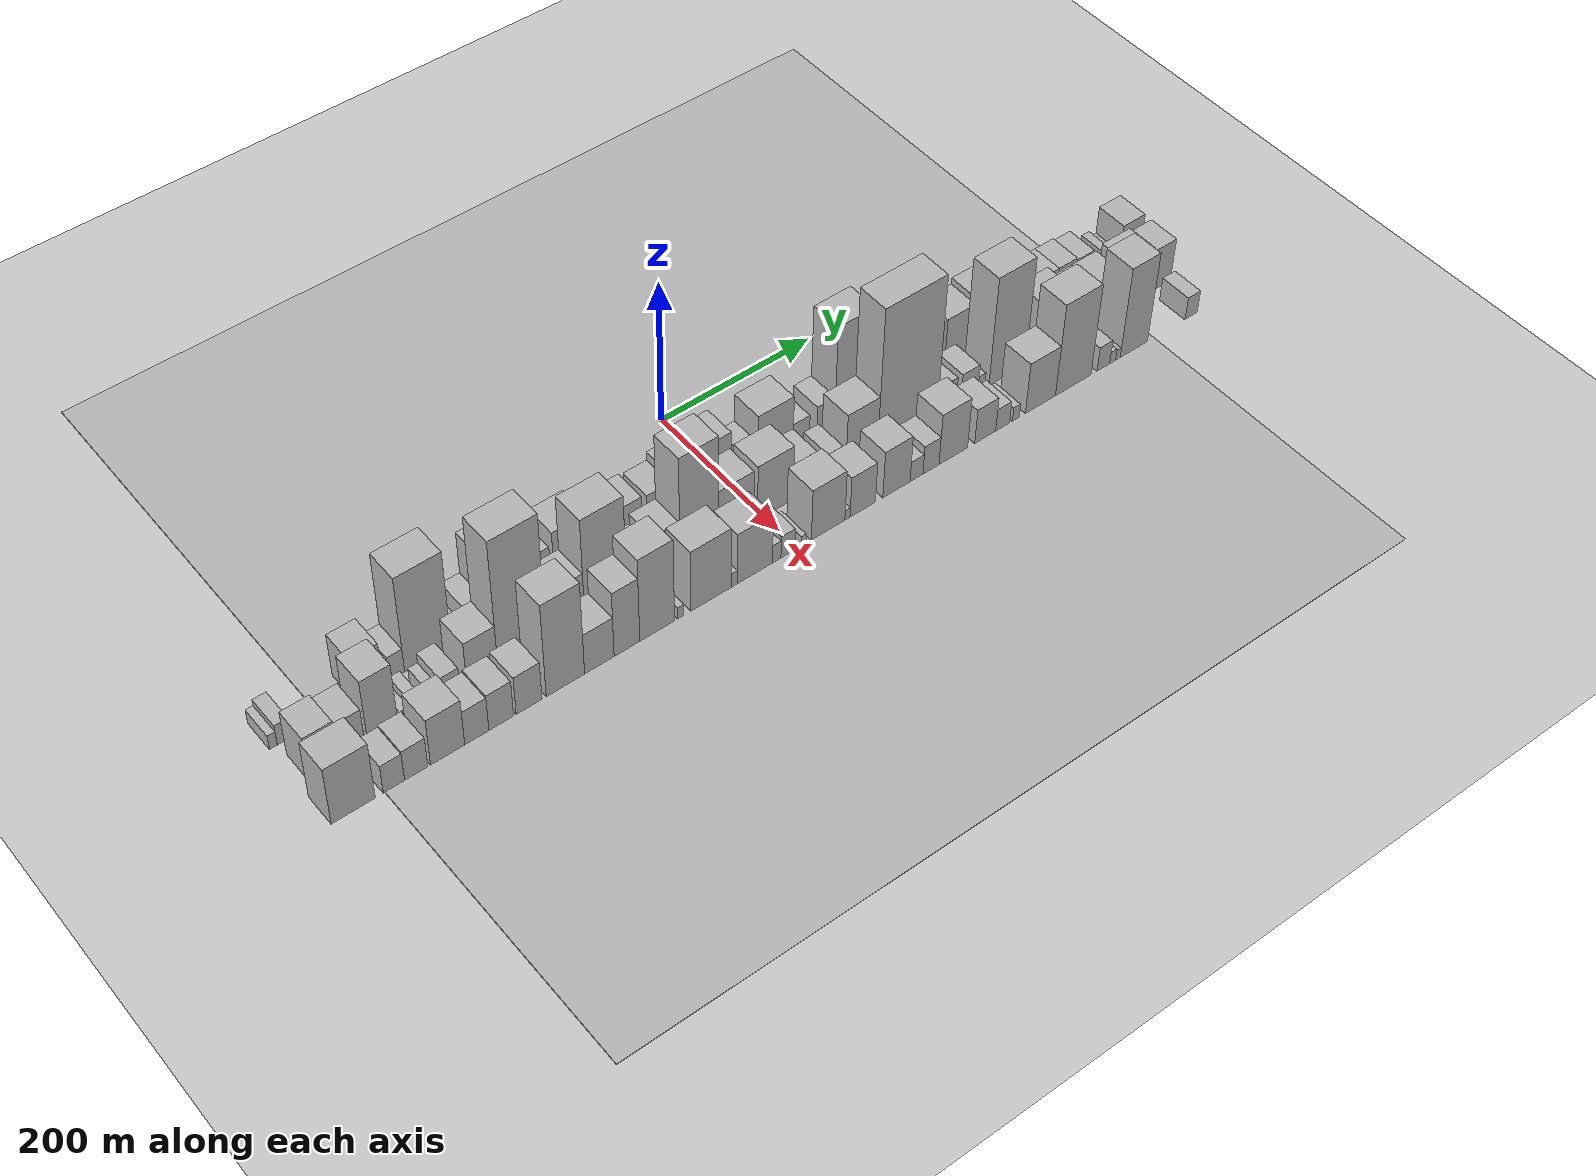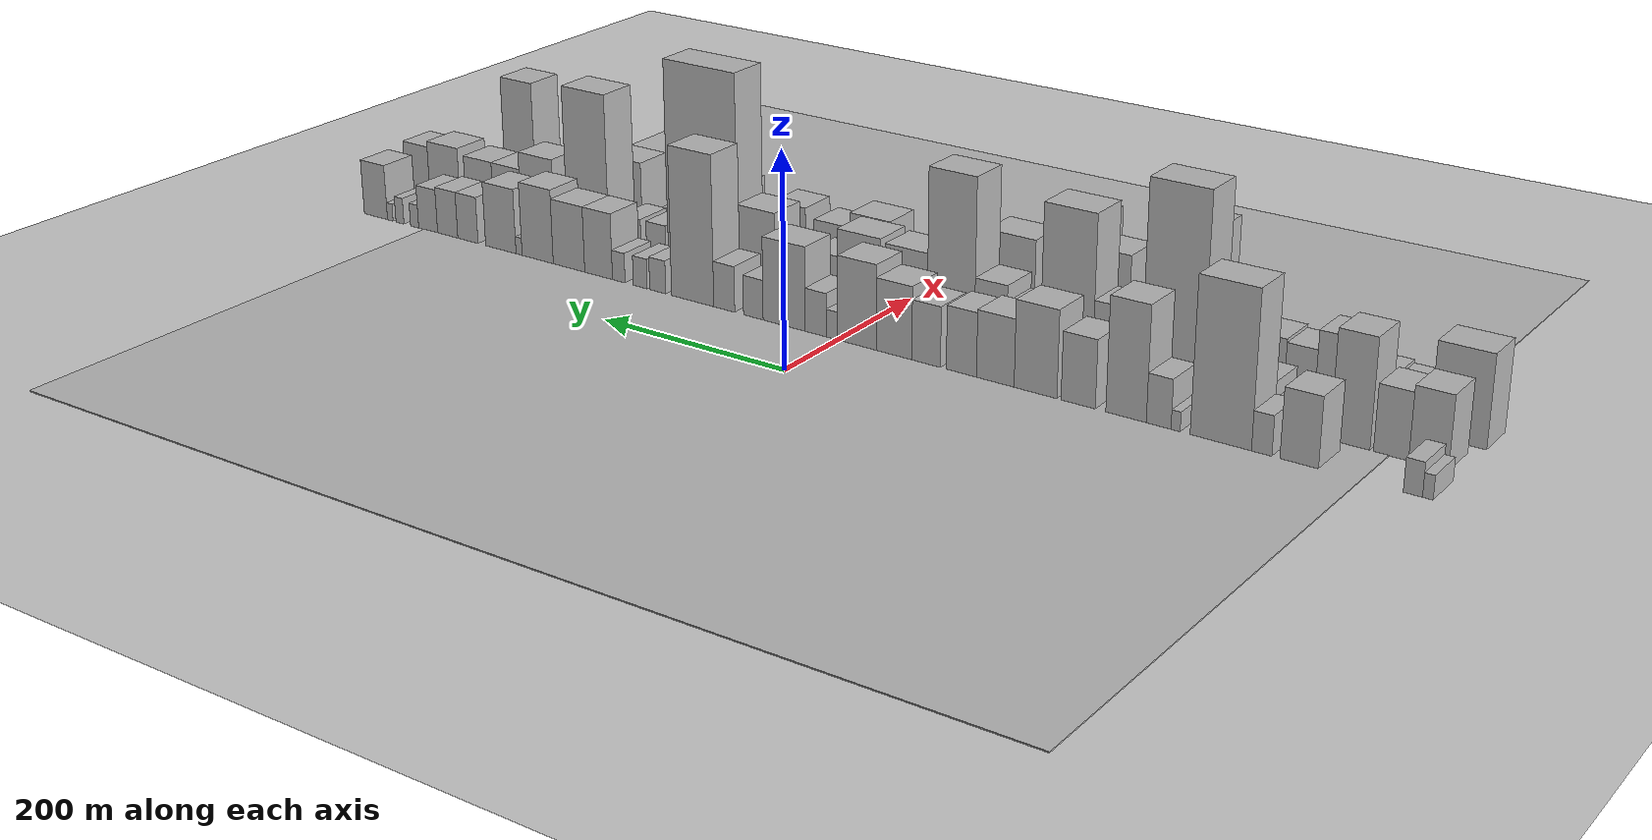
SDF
<?xml version="1.0" encoding="utf-8"?>

<sdf version="1.6">

   <world name="default">

      <gui fullscreen="0">

         <camera name="user_camera">

            <pose>-15 0 4.57585 0 0 0</pose>

            <view_controller>orbit</view_controller>

         </camera>

      </gui>

      <scene>

         <sky>

           <clouds>

             <speed>12</speed>

           </clouds>

         </sky>

         <ambient>0.4 0.4 0.4 1</ambient>

         <background>0.7 0.7 0.7 1</background>

         <shadows>1</shadows>

      </scene>

      <gravity>0 0 -9.8066</gravity>

      <magnetic_field>6e-06 2.3e-05 -4.2e-05</magnetic_field>

      <physics default="0" name="default_physics" type="ode">

         <ode>

            <solver>

               <type>quick</type>

               <iters>10</iters>

               <sor>1.0</sor>

               <use_dynamic_moi_rescaling>0</use_dynamic_moi_rescaling>

            </solver>

            <constraints>

               <cfm>0</cfm>

               <erp>0.2</erp>

               <contact_max_correcting_vel>100</contact_max_correcting_vel>

               <contact_surface_layer>0.001</contact_surface_layer>

            </constraints>

         </ode>

         <max_step_size>0.004</max_step_size>

         <real_time_factor>1</real_time_factor>

         <real_time_update_rate>250</real_time_update_rate>

      </physics>

      <light name="sun" type="directional">

         <cast_shadows>1</cast_shadows>

         <pose>0 0 10 0 0 0</pose>

         <diffuse>0.8 0.8 0.8 1</diffuse>

         <specular>0.2 0.2 0.2 1</specular>

         <attenuation>

            <range>1000</range>

            <constant>0.9</constant>

            <linear>0.01</linear>

            <quadratic>0.001</quadratic>

         </attenuation>

         <direction>-0.5 0.1 -0.9</direction>

      </light>

      <include>

         <name>ground_plane_1</name>

         <uri>model://HANNAS_ground_plane</uri>

         <pose>0 0 0  0 0 0</pose>

      </include>

      <include>

         <name>ground_plane_2</name>

         <uri>model://HANNAS_ground_plane</uri>

         <pose>100 0 0  0 0 0</pose>

      </include>

      <model name="building_1">

         <static>1</static>

         <pose frame="">100.0000 -555.5974 0 0.000000 0.000000 0.000000</pose>

         <link name="link">

            <pose frame="">0 0 10.50 0 0 0</pose>

            <collision name="collision">

               <geometry>

                  <box>

                     <size>40.0000 8.8052 21.0000</size>

                  </box>

               </geometry>

               <max_contacts>10</max_contacts>

               <surface>

                  <contact>

                     <ode/>

                  </contact>

                  <bounce/>

                  <friction>

                     <torsional>

                        <ode/>

                     </torsional>

                     <ode/>

                  </friction>

               </surface>

            </collision>

            <visual name="visual">

               <cast_shadows>0</cast_shadows>

               <geometry>

                  <box>

                     <size>40.0000 8.8052 21.0000</size>

                  </box>

               </geometry>

               <material>

                  <script>

                     <uri>model://HANNAS_wall/materials/scripts</uri>

                     <uri>model://HANNAS_wall/materials/textures</uri>

                     <name>vrc/HANNAS_wall</name>

                  </script>

               </material>

            </visual>

            <self_collide>0</self_collide>

            <enable_wind>0</enable_wind>

            <kinematic>0</kinematic>

         </link>

      </model>

      <model name="building_2">

         <static>1</static>

         <pose frame="">100.0000 -543.2743 0 0.000000 0.000000 0.000000</pose>

         <link name="link">

            <pose frame="">0 0 15.00 0 0 0</pose>

            <collision name="collision">

               <geometry>

                  <box>

                     <size>40.0000 15.8411 30.0000</size>

                  </box>

               </geometry>

               <max_contacts>10</max_contacts>

               <surface>

                  <contact>

                     <ode/>

                  </contact>

                  <bounce/>

                  <friction>

                     <torsional>

                        <ode/>

                     </torsional>

                     <ode/>

                  </friction>

               </surface>

            </collision>

            <visual name="visual">

               <cast_shadows>0</cast_shadows>

               <geometry>

                  <box>

                     <size>40.0000 15.8411 30.0000</size>

                  </box>

               </geometry>

               <material>

                  <script>

                     <uri>model://HANNAS_wall/materials/scripts</uri>

                     <uri>model://HANNAS_wall/materials/textures</uri>

                     <name>vrc/HANNAS_wall</name>

                  </script>

               </material>

            </visual>

            <self_collide>0</self_collide>

            <enable_wind>0</enable_wind>

            <kinematic>0</kinematic>

         </link>

      </model>

      <model name="building_3">

         <static>1</static>

         <pose frame="">100.0000 -447.1640 0 0.000000 0.000000 0.000000</pose>

         <link name="link">

            <pose frame="">0 0 31.50 0 0 0</pose>

            <collision name="collision">

               <geometry>

                  <box>

                     <size>40.0000 33.4599 63.0000</size>

                  </box>

               </geometry>

               <max_contacts>10</max_contacts>

               <surface>

                  <contact>

                     <ode/>

                  </contact>

                  <bounce/>

                  <friction>

                     <torsional>

                        <ode/>

                     </torsional>

                     <ode/>

                  </friction>

               </surface>

            </collision>

            <visual name="visual">

               <cast_shadows>0</cast_shadows>

               <geometry>

                  <box>

                     <size>40.0000 33.4599 63.0000</size>

                  </box>

               </geometry>

               <material>

                  <script>

                     <uri>model://HANNAS_wall/materials/scripts</uri>

                     <uri>model://HANNAS_wall/materials/textures</uri>

                     <name>vrc/HANNAS_wall</name>

                  </script>

               </material>

            </visual>

            <self_collide>0</self_collide>

            <enable_wind>0</enable_wind>

            <kinematic>0</kinematic>

         </link>

      </model>

      <model name="building_4">

         <static>1</static>

         <pose frame="">100.0000 -414.4182 0 0.000000 0.000000 0.000000</pose>

         <link name="link">

            <pose frame="">0 0 18.00 0 0 0</pose>

            <collision name="collision">

               <geometry>

                  <box>

                     <size>40.0000 18.0316 36.0000</size>

                  </box>

               </geometry>

               <max_contacts>10</max_contacts>

               <surface>

                  <contact>

                     <ode/>

                  </contact>

                  <bounce/>

                  <friction>

                     <torsional>

                        <ode/>

                     </torsional>

                     <ode/>

                  </friction>

               </surface>

            </collision>

            <visual name="visual">

               <cast_shadows>0</cast_shadows>

               <geometry>

                  <box>

                     <size>40.0000 18.0316 36.0000</size>

                  </box>

               </geometry>

               <material>

                  <script>

                     <uri>model://HANNAS_wall/materials/scripts</uri>

                     <uri>model://HANNAS_wall/materials/textures</uri>

                     <name>vrc/HANNAS_wall</name>

                  </script>

               </material>

            </visual>

            <self_collide>0</self_collide>

            <enable_wind>0</enable_wind>

            <kinematic>0</kinematic>

         </link>

      </model>

      <model name="building_5">

         <static>1</static>

         <pose frame="">100.0000 -377.8310 0 0.000000 0.000000 0.000000</pose>

         <link name="link">

            <pose frame="">0 0 70.50 0 0 0</pose>

            <collision name="collision">

               <geometry>

                  <box>

                     <size>40.0000 55.1429 141.0000</size>

                  </box>

               </geometry>

               <max_contacts>10</max_contacts>

               <surface>

                  <contact>

                     <ode/>

                  </contact>

                  <bounce/>

                  <friction>

                     <torsional>

                        <ode/>

                     </torsional>

                     <ode/>

                  </friction>

               </surface>

            </collision>

            <visual name="visual">

               <cast_shadows>0</cast_shadows>

               <geometry>

                  <box>

                     <size>40.0000 55.1429 141.0000</size>

                  </box>

               </geometry>

               <material>

                  <script>

                     <uri>model://HANNAS_wall/materials/scripts</uri>

                     <uri>model://HANNAS_wall/materials/textures</uri>

                     <name>vrc/HANNAS_wall</name>

                  </script>

               </material>

            </visual>

            <self_collide>0</self_collide>

            <enable_wind>0</enable_wind>

            <kinematic>0</kinematic>

         </link>

      </model>

      <model name="building_6">

         <static>1</static>

         <pose frame="">100.0000 -337.0304 0 0.000000 0.000000 0.000000</pose>

         <link name="link">

            <pose frame="">0 0 9.00 0 0 0</pose>

            <collision name="collision">

               <geometry>

                  <box>

                     <size>40.0000 8.4583 18.0000</size>

                  </box>

               </geometry>

               <max_contacts>10</max_contacts>

               <surface>

                  <contact>

                     <ode/>

                  </contact>

                  <bounce/>

                  <friction>

                     <torsional>

                        <ode/>

                     </torsional>

                     <ode/>

                  </friction>

               </surface>

            </collision>

            <visual name="visual">

               <cast_shadows>0</cast_shadows>

               <geometry>

                  <box>

                     <size>40.0000 8.4583 18.0000</size>

                  </box>

               </geometry>

               <material>

                  <script>

                     <uri>model://HANNAS_wall/materials/scripts</uri>

                     <uri>model://HANNAS_wall/materials/textures</uri>

                     <name>vrc/HANNAS_wall</name>

                  </script>

               </material>

            </visual>

            <self_collide>0</self_collide>

            <enable_wind>0</enable_wind>

            <kinematic>0</kinematic>

         </link>

      </model>

      <model name="building_7">

         <static>1</static>

         <pose frame="">100.0000 -321.3310 0 0.000000 0.000000 0.000000</pose>

         <link name="link">

            <pose frame="">0 0 22.50 0 0 0</pose>

            <collision name="collision">

               <geometry>

                  <box>

                     <size>40.0000 22.9405 45.0000</size>

                  </box>

               </geometry>

               <max_contacts>10</max_contacts>

               <surface>

                  <contact>

                     <ode/>

                  </contact>

                  <bounce/>

                  <friction>

                     <torsional>

                        <ode/>

                     </torsional>

                     <ode/>

                  </friction>

               </surface>

            </collision>

            <visual name="visual">

               <cast_shadows>0</cast_shadows>

               <geometry>

                  <box>

                     <size>40.0000 22.9405 45.0000</size>

                  </box>

               </geometry>

               <material>

                  <script>

                     <uri>model://HANNAS_wall/materials/scripts</uri>

                     <uri>model://HANNAS_wall/materials/textures</uri>

                     <name>vrc/HANNAS_wall</name>

                  </script>

               </material>

            </visual>

            <self_collide>0</self_collide>

            <enable_wind>0</enable_wind>

            <kinematic>0</kinematic>

         </link>

      </model>

      <model name="building_8">

         <static>1</static>

         <pose frame="">100.0000 -290.8795 0 0.000000 0.000000 0.000000</pose>

         <link name="link">

            <pose frame="">0 0 52.50 0 0 0</pose>

            <collision name="collision">

               <geometry>

                  <box>

                     <size>40.0000 37.9624 105.0000</size>

                  </box>

               </geometry>

               <max_contacts>10</max_contacts>

               <surface>

                  <contact>

                     <ode/>

                  </contact>

                  <bounce/>

                  <friction>

                     <torsional>

                        <ode/>

                     </torsional>

                     <ode/>

                  </friction>

               </surface>

            </collision>

            <visual name="visual">

               <cast_shadows>0</cast_shadows>

               <geometry>

                  <box>

                     <size>40.0000 37.9624 105.0000</size>

                  </box>

               </geometry>

               <material>

                  <script>

                     <uri>model://HANNAS_wall/materials/scripts</uri>

                     <uri>model://HANNAS_wall/materials/textures</uri>

                     <name>vrc/HANNAS_wall</name>

                  </script>

               </material>

            </visual>

            <self_collide>0</self_collide>

            <enable_wind>0</enable_wind>

            <kinematic>0</kinematic>

         </link>

      </model>

      <model name="building_9">

         <static>1</static>

         <pose frame="">100.0000 -245.4455 0 0.000000 0.000000 0.000000</pose>

         <link name="link">

            <pose frame="">0 0 31.50 0 0 0</pose>

            <collision name="collision">

               <geometry>

                  <box>

                     <size>40.0000 32.9055 63.0000</size>

                  </box>

               </geometry>

               <max_contacts>10</max_contacts>

               <surface>

                  <contact>

                     <ode/>

                  </contact>

                  <bounce/>

                  <friction>

                     <torsional>

                        <ode/>

                     </torsional>

                     <ode/>

                  </friction>

               </surface>

            </collision>

            <visual name="visual">

               <cast_shadows>0</cast_shadows>

               <geometry>

                  <box>

                     <size>40.0000 32.9055 63.0000</size>

                  </box>

               </geometry>

               <material>

                  <script>

                     <uri>model://HANNAS_wall/materials/scripts</uri>

                     <uri>model://HANNAS_wall/materials/textures</uri>

                     <name>vrc/HANNAS_wall</name>

                  </script>

               </material>

            </visual>

            <self_collide>0</self_collide>

            <enable_wind>0</enable_wind>

            <kinematic>0</kinematic>

         </link>

      </model>

      <model name="building_10">

         <static>1</static>

         <pose frame="">100.0000 -203.9878 0 0.000000 0.000000 0.000000</pose>

         <link name="link">

            <pose frame="">0 0 40.50 0 0 0</pose>

            <collision name="collision">

               <geometry>

                  <box>

                     <size>40.0000 42.0099 81.0000</size>

                  </box>

               </geometry>

               <max_contacts>10</max_contacts>

               <surface>

                  <contact>

                     <ode/>

                  </contact>

                  <bounce/>

                  <friction>

                     <torsional>

                        <ode/>

                     </torsional>

                     <ode/>

                  </friction>

               </surface>

            </collision>

            <visual name="visual">

               <cast_shadows>0</cast_shadows>

               <geometry>

                  <box>

                     <size>40.0000 42.0099 81.0000</size>

                  </box>

               </geometry>

               <material>

                  <script>

                     <uri>model://HANNAS_wall/materials/scripts</uri>

                     <uri>model://HANNAS_wall/materials/textures</uri>

                     <name>vrc/HANNAS_wall</name>

                  </script>

               </material>

            </visual>

            <self_collide>0</self_collide>

            <enable_wind>0</enable_wind>

            <kinematic>0</kinematic>

         </link>

      </model>

      <model name="building_11">

         <static>1</static>

         <pose frame="">100.0000 -164.1223 0 0.000000 0.000000 0.000000</pose>

         <link name="link">

            <pose frame="">0 0 31.50 0 0 0</pose>

            <collision name="collision">

               <geometry>

                  <box>

                     <size>40.0000 37.7210 63.0000</size>

                  </box>

               </geometry>

               <max_contacts>10</max_contacts>

               <surface>

                  <contact>

                     <ode/>

                  </contact>

                  <bounce/>

                  <friction>

                     <torsional>

                        <ode/>

                     </torsional>

                     <ode/>

                  </friction>

               </surface>

            </collision>

            <visual name="visual">

               <cast_shadows>0</cast_shadows>

               <geometry>

                  <box>

                     <size>40.0000 37.7210 63.0000</size>

                  </box>

               </geometry>

               <material>

                  <script>

                     <uri>model://HANNAS_wall/materials/scripts</uri>

                     <uri>model://HANNAS_wall/materials/textures</uri>

                     <name>vrc/HANNAS_wall</name>

                  </script>

               </material>

            </visual>

            <self_collide>0</self_collide>

            <enable_wind>0</enable_wind>

            <kinematic>0</kinematic>

         </link>

      </model>

      <model name="building_12">

         <static>1</static>

         <pose frame="">100.0000 -129.9413 0 0.000000 0.000000 0.000000</pose>

         <link name="link">

            <pose frame="">0 0 30.00 0 0 0</pose>

            <collision name="collision">

               <geometry>

                  <box>

                     <size>40.0000 30.6410 60.0000</size>

                  </box>

               </geometry>

               <max_contacts>10</max_contacts>

               <surface>

                  <contact>

                     <ode/>

                  </contact>

                  <bounce/>

                  <friction>

                     <torsional>

                        <ode/>

                     </torsional>

                     <ode/>

                  </friction>

               </surface>

            </collision>

            <visual name="visual">

               <cast_shadows>0</cast_shadows>

               <geometry>

                  <box>

                     <size>40.0000 30.6410 60.0000</size>

                  </box>

               </geometry>

               <material>

                  <script>

                     <uri>model://HANNAS_wall/materials/scripts</uri>

                     <uri>model://HANNAS_wall/materials/textures</uri>

                     <name>vrc/HANNAS_wall</name>

                  </script>

               </material>

            </visual>

            <self_collide>0</self_collide>

            <enable_wind>0</enable_wind>

            <kinematic>0</kinematic>

         </link>

      </model>

      <model name="building_13">

         <static>1</static>

         <pose frame="">100.0000 -93.8213 0 0.000000 0.000000 0.000000</pose>

         <link name="link">

            <pose frame="">0 0 28.50 0 0 0</pose>

            <collision name="collision">

               <geometry>

                  <box>

                     <size>40.0000 29.5989 57.0000</size>

                  </box>

               </geometry>

               <max_contacts>10</max_contacts>

               <surface>

                  <contact>

                     <ode/>

                  </contact>

                  <bounce/>

                  <friction>

                     <torsional>

                        <ode/>

                     </torsional>

                     <ode/>

                  </friction>

               </surface>

            </collision>

            <visual name="visual">

               <cast_shadows>0</cast_shadows>

               <geometry>

                  <box>

                     <size>40.0000 29.5989 57.0000</size>

                  </box>

               </geometry>

               <material>

                  <script>

                     <uri>model://HANNAS_wall/materials/scripts</uri>

                     <uri>model://HANNAS_wall/materials/textures</uri>

                     <name>vrc/HANNAS_wall</name>

                  </script>

               </material>

            </visual>

            <self_collide>0</self_collide>

            <enable_wind>0</enable_wind>

            <kinematic>0</kinematic>

         </link>

      </model>

      <model name="building_14">

         <static>1</static>

         <pose frame="">100.0000 -60.3481 0 0.000000 0.000000 0.000000</pose>

         <link name="link">

            <pose frame="">0 0 34.50 0 0 0</pose>

            <collision name="collision">

               <geometry>

                  <box>

                     <size>40.0000 37.3476 69.0000</size>

                  </box>

               </geometry>

               <max_contacts>10</max_contacts>

               <surface>

                  <contact>

                     <ode/>

                  </contact>

                  <bounce/>

                  <friction>

                     <torsional>

                        <ode/>

                     </torsional>

                     <ode/>

                  </friction>

               </surface>

            </collision>

            <visual name="visual">

               <cast_shadows>0</cast_shadows>

               <geometry>

                  <box>

                     <size>40.0000 37.3476 69.0000</size>

                  </box>

               </geometry>

               <material>

                  <script>

                     <uri>model://HANNAS_wall/materials/scripts</uri>

                     <uri>model://HANNAS_wall/materials/textures</uri>

                     <name>vrc/HANNAS_wall</name>

                  </script>

               </material>

            </visual>

            <self_collide>0</self_collide>

            <enable_wind>0</enable_wind>

            <kinematic>0</kinematic>

         </link>

      </model>

      <model name="building_15">

         <static>1</static>

         <pose frame="">100.0000 -20.8964 0 0.000000 0.000000 0.000000</pose>

         <link name="link">

            <pose frame="">0 0 40.50 0 0 0</pose>

            <collision name="collision">

               <geometry>

                  <box>

                     <size>40.0000 41.5558 81.0000</size>

                  </box>

               </geometry>

               <max_contacts>10</max_contacts>

               <surface>

                  <contact>

                     <ode/>

                  </contact>

                  <bounce/>

                  <friction>

                     <torsional>

                        <ode/>

                     </torsional>

                     <ode/>

                  </friction>

               </surface>

            </collision>

            <visual name="visual">

               <cast_shadows>0</cast_shadows>

               <geometry>

                  <box>

                     <size>40.0000 41.5558 81.0000</size>

                  </box>

               </geometry>

               <material>

                  <script>

                     <uri>model://HANNAS_wall/materials/scripts</uri>

                     <uri>model://HANNAS_wall/materials/textures</uri>

                     <name>vrc/HANNAS_wall</name>

                  </script>

               </material>

            </visual>

            <self_collide>0</self_collide>

            <enable_wind>0</enable_wind>

            <kinematic>0</kinematic>

         </link>

      </model>

      <model name="building_16">

         <static>1</static>

         <pose frame="">100.0000 6.0256 0 0.000000 0.000000 0.000000</pose>

         <link name="link">

            <pose frame="">0 0 13.50 0 0 0</pose>

            <collision name="collision">

               <geometry>

                  <box>

                     <size>40.0000 12.2881 27.0000</size>

                  </box>

               </geometry>

               <max_contacts>10</max_contacts>

               <surface>

                  <contact>

                     <ode/>

                  </contact>

                  <bounce/>

                  <friction>

                     <torsional>

                        <ode/>

                     </torsional>

                     <ode/>

                  </friction>

               </surface>

            </collision>

            <visual name="visual">

               <cast_shadows>0</cast_shadows>

               <geometry>

                  <box>

                     <size>40.0000 12.2881 27.0000</size>

                  </box>

               </geometry>

               <material>

                  <script>

                     <uri>model://HANNAS_wall/materials/scripts</uri>

                     <uri>model://HANNAS_wall/materials/textures</uri>

                     <name>vrc/HANNAS_wall</name>

                  </script>

               </material>

            </visual>

            <self_collide>0</self_collide>

            <enable_wind>0</enable_wind>

            <kinematic>0</kinematic>

         </link>

      </model>

      <model name="building_17">

         <static>1</static>

         <pose frame="">100.0000 23.6727 0 0.000000 0.000000 0.000000</pose>

         <link name="link">

            <pose frame="">0 0 21.00 0 0 0</pose>

            <collision name="collision">

               <geometry>

                  <box>

                     <size>40.0000 23.0060 42.0000</size>

                  </box>

               </geometry>

               <max_contacts>10</max_contacts>

               <surface>

                  <contact>

                     <ode/>

                  </contact>

                  <bounce/>

                  <friction>

                     <torsional>

                        <ode/>

                     </torsional>

                     <ode/>

                  </friction>

               </surface>

            </collision>

            <visual name="visual">

               <cast_shadows>0</cast_shadows>

               <geometry>

                  <box>

                     <size>40.0000 23.0060 42.0000</size>

                  </box>

               </geometry>

               <material>

                  <script>

                     <uri>model://HANNAS_wall/materials/scripts</uri>

                     <uri>model://HANNAS_wall/materials/textures</uri>

                     <name>vrc/HANNAS_wall</name>

                  </script>

               </material>

            </visual>

            <self_collide>0</self_collide>

            <enable_wind>0</enable_wind>

            <kinematic>0</kinematic>

         </link>

      </model>

      <model name="building_18">

         <static>1</static>

         <pose frame="">100.0000 58.6374 0 0.000000 0.000000 0.000000</pose>

         <link name="link">

            <pose frame="">0 0 40.50 0 0 0</pose>

            <collision name="collision">

               <geometry>

                  <box>

                     <size>40.0000 46.9235 81.0000</size>

                  </box>

               </geometry>

               <max_contacts>10</max_contacts>

               <surface>

                  <contact>

                     <ode/>

                  </contact>

                  <bounce/>

                  <friction>

                     <torsional>

                        <ode/>

                     </torsional>

                     <ode/>

                  </friction>

               </surface>

            </collision>

            <visual name="visual">

               <cast_shadows>0</cast_shadows>

               <geometry>

                  <box>

                     <size>40.0000 46.9235 81.0000</size>

                  </box>

               </geometry>

               <material>

                  <script>

                     <uri>model://HANNAS_wall/materials/scripts</uri>

                     <uri>model://HANNAS_wall/materials/textures</uri>

                     <name>vrc/HANNAS_wall</name>

                  </script>

               </material>

            </visual>

            <self_collide>0</self_collide>

            <enable_wind>0</enable_wind>

            <kinematic>0</kinematic>

         </link>

      </model>

      <model name="building_19">

         <static>1</static>

         <pose frame="">100.0000 93.1866 0 0.000000 0.000000 0.000000</pose>

         <link name="link">

            <pose frame="">0 0 19.50 0 0 0</pose>

            <collision name="collision">

               <geometry>

                  <box>

                     <size>40.0000 22.1749 39.0000</size>

                  </box>

               </geometry>

               <max_contacts>10</max_contacts>

               <surface>

                  <contact>

                     <ode/>

                  </contact>

                  <bounce/>

                  <friction>

                     <torsional>

                        <ode/>

                     </torsional>

                     <ode/>

                  </friction>

               </surface>

            </collision>

            <visual name="visual">

               <cast_shadows>0</cast_shadows>

               <geometry>

                  <box>

                     <size>40.0000 22.1749 39.0000</size>

                  </box>

               </geometry>

               <material>

                  <script>

                     <uri>model://HANNAS_wall/materials/scripts</uri>

                     <uri>model://HANNAS_wall/materials/textures</uri>

                     <name>vrc/HANNAS_wall</name>

                  </script>

               </material>

            </visual>

            <self_collide>0</self_collide>

            <enable_wind>0</enable_wind>

            <kinematic>0</kinematic>

         </link>

      </model>

      <model name="building_20">

         <static>1</static>

         <pose frame="">100.0000 126.3091 0 0.000000 0.000000 0.000000</pose>

         <link name="link">

            <pose frame="">0 0 22.50 0 0 0</pose>

            <collision name="collision">

               <geometry>

                  <box>

                     <size>40.0000 24.0701 45.0000</size>

                  </box>

               </geometry>

               <max_contacts>10</max_contacts>

               <surface>

                  <contact>

                     <ode/>

                  </contact>

                  <bounce/>

                  <friction>

                     <torsional>

                        <ode/>

                     </torsional>

                     <ode/>

                  </friction>

               </surface>

            </collision>

            <visual name="visual">

               <cast_shadows>0</cast_shadows>

               <geometry>

                  <box>

                     <size>40.0000 24.0701 45.0000</size>

                  </box>

               </geometry>

               <material>

                  <script>

                     <uri>model://HANNAS_wall/materials/scripts</uri>

                     <uri>model://HANNAS_wall/materials/textures</uri>

                     <name>vrc/HANNAS_wall</name>

                  </script>

               </material>

            </visual>

            <self_collide>0</self_collide>

            <enable_wind>0</enable_wind>

            <kinematic>0</kinematic>

         </link>

      </model>

      <model name="building_21">

         <static>1</static>

         <pose frame="">100.0000 162.9610 0 0.000000 0.000000 0.000000</pose>

         <link name="link">

            <pose frame="">0 0 73.50 0 0 0</pose>

            <collision name="collision">

               <geometry>

                  <box>

                     <size>40.0000 49.2336 147.0000</size>

                  </box>

               </geometry>

               <max_contacts>10</max_contacts>

               <surface>

                  <contact>

                     <ode/>

                  </contact>

                  <bounce/>

                  <friction>

                     <torsional>

                        <ode/>

                     </torsional>

                     <ode/>

                  </friction>

               </surface>

            </collision>

            <visual name="visual">

               <cast_shadows>0</cast_shadows>

               <geometry>

                  <box>

                     <size>40.0000 49.2336 147.0000</size>

                  </box>

               </geometry>

               <material>

                  <script>

                     <uri>model://HANNAS_wall/materials/scripts</uri>

                     <uri>model://HANNAS_wall/materials/textures</uri>

                     <name>vrc/HANNAS_wall</name>

                  </script>

               </material>

            </visual>

            <self_collide>0</self_collide>

            <enable_wind>0</enable_wind>

            <kinematic>0</kinematic>

         </link>

      </model>

      <model name="building_22">

         <static>1</static>

         <pose frame="">100.0000 204.0887 0 0.000000 0.000000 0.000000</pose>

         <link name="link">

            <pose frame="">0 0 16.50 0 0 0</pose>

            <collision name="collision">

               <geometry>

                  <box>

                     <size>40.0000 19.0217 33.0000</size>

                  </box>

               </geometry>

               <max_contacts>10</max_contacts>

               <surface>

                  <contact>

                     <ode/>

                  </contact>

                  <bounce/>

                  <friction>

                     <torsional>

                        <ode/>

                     </torsional>

                     <ode/>

                  </friction>

               </surface>

            </collision>

            <visual name="visual">

               <cast_shadows>0</cast_shadows>

               <geometry>

                  <box>

                     <size>40.0000 19.0217 33.0000</size>

                  </box>

               </geometry>

               <material>

                  <script>

                     <uri>model://HANNAS_wall/materials/scripts</uri>

                     <uri>model://HANNAS_wall/materials/textures</uri>

                     <name>vrc/HANNAS_wall</name>

                  </script>

               </material>

            </visual>

            <self_collide>0</self_collide>

            <enable_wind>0</enable_wind>

            <kinematic>0</kinematic>

         </link>

      </model>

      <model name="building_23">

         <static>1</static>

         <pose frame="">100.0000 224.9152 0 0.000000 0.000000 0.000000</pose>

         <link name="link">

            <pose frame="">0 0 15.00 0 0 0</pose>

            <collision name="collision">

               <geometry>

                  <box>

                     <size>40.0000 16.6313 30.0000</size>

                  </box>

               </geometry>

               <max_contacts>10</max_contacts>

               <surface>

                  <contact>

                     <ode/>

                  </contact>

                  <bounce/>

                  <friction>

                     <torsional>

                        <ode/>

                     </torsional>

                     <ode/>

                  </friction>

               </surface>

            </collision>

            <visual name="visual">

               <cast_shadows>0</cast_shadows>

               <geometry>

                  <box>

                     <size>40.0000 16.6313 30.0000</size>

                  </box>

               </geometry>

               <material>

                  <script>

                     <uri>model://HANNAS_wall/materials/scripts</uri>

                     <uri>model://HANNAS_wall/materials/textures</uri>

                     <name>vrc/HANNAS_wall</name>

                  </script>

               </material>

            </visual>

            <self_collide>0</self_collide>

            <enable_wind>0</enable_wind>

            <kinematic>0</kinematic>

         </link>

      </model>

      <model name="building_24">

         <static>1</static>

         <pose frame="">100.0000 250.9024 0 0.000000 0.000000 0.000000</pose>

         <link name="link">

            <pose frame="">0 0 15.00 0 0 0</pose>

            <collision name="collision">

               <geometry>

                  <box>

                     <size>40.0000 15.3431 30.0000</size>

                  </box>

               </geometry>

               <max_contacts>10</max_contacts>

               <surface>

                  <contact>

                     <ode/>

                  </contact>

                  <bounce/>

                  <friction>

                     <torsional>

                        <ode/>

                     </torsional>

                     <ode/>

                  </friction>

               </surface>

            </collision>

            <visual name="visual">

               <cast_shadows>0</cast_shadows>

               <geometry>

                  <box>

                     <size>40.0000 15.3431 30.0000</size>

                  </box>

               </geometry>

               <material>

                  <script>

                     <uri>model://HANNAS_wall/materials/scripts</uri>

                     <uri>model://HANNAS_wall/materials/textures</uri>

                     <name>vrc/HANNAS_wall</name>

                  </script>

               </material>

            </visual>

            <self_collide>0</self_collide>

            <enable_wind>0</enable_wind>

            <kinematic>0</kinematic>

         </link>

      </model>

      <model name="building_25">

         <static>1</static>

         <pose frame="">100.0000 275.6220 0 0.000000 0.000000 0.000000</pose>

         <link name="link">

            <pose frame="">0 0 33.00 0 0 0</pose>

            <collision name="collision">

               <geometry>

                  <box>

                     <size>40.0000 34.0961 66.0000</size>

                  </box>

               </geometry>

               <max_contacts>10</max_contacts>

               <surface>

                  <contact>

                     <ode/>

                  </contact>

                  <bounce/>

                  <friction>

                     <torsional>

                        <ode/>

                     </torsional>

                     <ode/>

                  </friction>

               </surface>

            </collision>

            <visual name="visual">

               <cast_shadows>0</cast_shadows>

               <geometry>

                  <box>

                     <size>40.0000 34.0961 66.0000</size>

                  </box>

               </geometry>

               <material>

                  <script>

                     <uri>model://HANNAS_wall/materials/scripts</uri>

                     <uri>model://HANNAS_wall/materials/textures</uri>

                     <name>vrc/HANNAS_wall</name>

                  </script>

               </material>

            </visual>

            <self_collide>0</self_collide>

            <enable_wind>0</enable_wind>

            <kinematic>0</kinematic>

         </link>

      </model>

      <model name="building_26">

         <static>1</static>

         <pose frame="">100.0000 312.3121 0 0.000000 0.000000 0.000000</pose>

         <link name="link">

            <pose frame="">0 0 33.00 0 0 0</pose>

            <collision name="collision">

               <geometry>

                  <box>

                     <size>40.0000 39.2841 66.0000</size>

                  </box>

               </geometry>

               <max_contacts>10</max_contacts>

               <surface>

                  <contact>

                     <ode/>

                  </contact>

                  <bounce/>

                  <friction>

                     <torsional>

                        <ode/>

                     </torsional>

                     <ode/>

                  </friction>

               </surface>

            </collision>

            <visual name="visual">

               <cast_shadows>0</cast_shadows>

               <geometry>

                  <box>

                     <size>40.0000 39.2841 66.0000</size>

                  </box>

               </geometry>

               <material>

                  <script>

                     <uri>model://HANNAS_wall/materials/scripts</uri>

                     <uri>model://HANNAS_wall/materials/textures</uri>

                     <name>vrc/HANNAS_wall</name>

                  </script>

               </material>

            </visual>

            <self_collide>0</self_collide>

            <enable_wind>0</enable_wind>

            <kinematic>0</kinematic>

         </link>

      </model>

      <model name="building_27">

         <static>1</static>

         <pose frame="">100.0000 351.7516 0 0.000000 0.000000 0.000000</pose>

         <link name="link">

            <pose frame="">0 0 37.50 0 0 0</pose>

            <collision name="collision">

               <geometry>

                  <box>

                     <size>40.0000 39.5950 75.0000</size>

                  </box>

               </geometry>

               <max_contacts>10</max_contacts>

               <surface>

                  <contact>

                     <ode/>

                  </contact>

                  <bounce/>

                  <friction>

                     <torsional>

                        <ode/>

                     </torsional>

                     <ode/>

                  </friction>

               </surface>

            </collision>

            <visual name="visual">

               <cast_shadows>0</cast_shadows>

               <geometry>

                  <box>

                     <size>40.0000 39.5950 75.0000</size>

                  </box>

               </geometry>

               <material>

                  <script>

                     <uri>model://HANNAS_wall/materials/scripts</uri>

                     <uri>model://HANNAS_wall/materials/textures</uri>

                     <name>vrc/HANNAS_wall</name>

                  </script>

               </material>

            </visual>

            <self_collide>0</self_collide>

            <enable_wind>0</enable_wind>

            <kinematic>0</kinematic>

         </link>

      </model>

      <model name="building_28">

         <static>1</static>

         <pose frame="">100.0000 375.4335 0 0.000000 0.000000 0.000000</pose>

         <link name="link">

            <pose frame="">0 0 9.00 0 0 0</pose>

            <collision name="collision">

               <geometry>

                  <box>

                     <size>40.0000 7.7689 18.0000</size>

                  </box>

               </geometry>

               <max_contacts>10</max_contacts>

               <surface>

                  <contact>

                     <ode/>

                  </contact>

                  <bounce/>

                  <friction>

                     <torsional>

                        <ode/>

                     </torsional>

                     <ode/>

                  </friction>

               </surface>

            </collision>

            <visual name="visual">

               <cast_shadows>0</cast_shadows>

               <geometry>

                  <box>

                     <size>40.0000 7.7689 18.0000</size>

                  </box>

               </geometry>

               <material>

                  <script>

                     <uri>model://HANNAS_wall/materials/scripts</uri>

                     <uri>model://HANNAS_wall/materials/textures</uri>

                     <name>vrc/HANNAS_wall</name>

                  </script>

               </material>

            </visual>

            <self_collide>0</self_collide>

            <enable_wind>0</enable_wind>

            <kinematic>0</kinematic>

         </link>

      </model>

      <model name="building_29">

         <static>1</static>

         <pose frame="">100.0000 399.0089 0 0.000000 0.000000 0.000000</pose>

         <link name="link">

            <pose frame="">0 0 33.00 0 0 0</pose>

            <collision name="collision">

               <geometry>

                  <box>

                     <size>40.0000 39.3817 66.0000</size>

                  </box>

               </geometry>

               <max_contacts>10</max_contacts>

               <surface>

                  <contact>

                     <ode/>

                  </contact>

                  <bounce/>

                  <friction>

                     <torsional>

                        <ode/>

                     </torsional>

                     <ode/>

                  </friction>

               </surface>

            </collision>

            <visual name="visual">

               <cast_shadows>0</cast_shadows>

               <geometry>

                  <box>

                     <size>40.0000 39.3817 66.0000</size>

                  </box>

               </geometry>

               <material>

                  <script>

                     <uri>model://HANNAS_wall/materials/scripts</uri>

                     <uri>model://HANNAS_wall/materials/textures</uri>

                     <name>vrc/HANNAS_wall</name>

                  </script>

               </material>

            </visual>

            <self_collide>0</self_collide>

            <enable_wind>0</enable_wind>

            <kinematic>0</kinematic>

         </link>

      </model>

      <model name="building_30">

         <static>1</static>

         <pose frame="">100.0000 442.0550 0 0.000000 0.000000 0.000000</pose>

         <link name="link">

            <pose frame="">0 0 24.00 0 0 0</pose>

            <collision name="collision">

               <geometry>

                  <box>

                     <size>40.0000 26.7106 48.0000</size>

                  </box>

               </geometry>

               <max_contacts>10</max_contacts>

               <surface>

                  <contact>

                     <ode/>

                  </contact>

                  <bounce/>

                  <friction>

                     <torsional>

                        <ode/>

                     </torsional>

                     <ode/>

                  </friction>

               </surface>

            </collision>

            <visual name="visual">

               <cast_shadows>0</cast_shadows>

               <geometry>

                  <box>

                     <size>40.0000 26.7106 48.0000</size>

                  </box>

               </geometry>

               <material>

                  <script>

                     <uri>model://HANNAS_wall/materials/scripts</uri>

                     <uri>model://HANNAS_wall/materials/textures</uri>

                     <name>vrc/HANNAS_wall</name>

                  </script>

               </material>

            </visual>

            <self_collide>0</self_collide>

            <enable_wind>0</enable_wind>

            <kinematic>0</kinematic>

         </link>

      </model>

      <model name="building_31">

         <static>1</static>

         <pose frame="">100.0000 468.9195 0 0.000000 0.000000 0.000000</pose>

         <link name="link">

            <pose frame="">0 0 24.00 0 0 0</pose>

            <collision name="collision">

               <geometry>

                  <box>

                     <size>40.0000 27.0183 48.0000</size>

                  </box>

               </geometry>

               <max_contacts>10</max_contacts>

               <surface>

                  <contact>

                     <ode/>

                  </contact>

                  <bounce/>

                  <friction>

                     <torsional>

                        <ode/>

                     </torsional>

                     <ode/>

                  </friction>

               </surface>

            </collision>

            <visual name="visual">

               <cast_shadows>0</cast_shadows>

               <geometry>

                  <box>

                     <size>40.0000 27.0183 48.0000</size>

                  </box>

               </geometry>

               <material>

                  <script>

                     <uri>model://HANNAS_wall/materials/scripts</uri>

                     <uri>model://HANNAS_wall/materials/textures</uri>

                     <name>vrc/HANNAS_wall</name>

                  </script>

               </material>

            </visual>

            <self_collide>0</self_collide>

            <enable_wind>0</enable_wind>

            <kinematic>0</kinematic>

         </link>

      </model>

      <model name="building_32">

         <static>1</static>

         <pose frame="">100.0000 495.2154 0 0.000000 0.000000 0.000000</pose>

         <link name="link">

            <pose frame="">0 0 22.50 0 0 0</pose>

            <collision name="collision">

               <geometry>

                  <box>

                     <size>40.0000 25.5737 45.0000</size>

                  </box>

               </geometry>

               <max_contacts>10</max_contacts>

               <surface>

                  <contact>

                     <ode/>

                  </contact>

                  <bounce/>

                  <friction>

                     <torsional>

                        <ode/>

                     </torsional>

                     <ode/>

                  </friction>

               </surface>

            </collision>

            <visual name="visual">

               <cast_shadows>0</cast_shadows>

               <geometry>

                  <box>

                     <size>40.0000 25.5737 45.0000</size>

                  </box>

               </geometry>

               <material>

                  <script>

                     <uri>model://HANNAS_wall/materials/scripts</uri>

                     <uri>model://HANNAS_wall/materials/textures</uri>

                     <name>vrc/HANNAS_wall</name>

                  </script>

               </material>

            </visual>

            <self_collide>0</self_collide>

            <enable_wind>0</enable_wind>

            <kinematic>0</kinematic>

         </link>

      </model>

      <model name="building_33">

         <static>1</static>

         <pose frame="">100.0000 513.5255 0 0.000000 0.000000 0.000000</pose>

         <link name="link">

            <pose frame="">0 0 12.00 0 0 0</pose>

            <collision name="collision">

               <geometry>

                  <box>

                     <size>40.0000 11.0465 24.0000</size>

                  </box>

               </geometry>

               <max_contacts>10</max_contacts>

               <surface>

                  <contact>

                     <ode/>

                  </contact>

                  <bounce/>

                  <friction>

                     <torsional>

                        <ode/>

                     </torsional>

                     <ode/>

                  </friction>

               </surface>

            </collision>

            <visual name="visual">

               <cast_shadows>0</cast_shadows>

               <geometry>

                  <box>

                     <size>40.0000 11.0465 24.0000</size>

                  </box>

               </geometry>

               <material>

                  <script>

                     <uri>model://HANNAS_wall/materials/scripts</uri>

                     <uri>model://HANNAS_wall/materials/textures</uri>

                     <name>vrc/HANNAS_wall</name>

                  </script>

               </material>

            </visual>

            <self_collide>0</self_collide>

            <enable_wind>0</enable_wind>

            <kinematic>0</kinematic>

         </link>

      </model>

      <model name="building_34">

         <static>1</static>

         <pose frame="">100.0000 533.5583 0 0.000000 0.000000 0.000000</pose>

         <link name="link">

            <pose frame="">0 0 13.50 0 0 0</pose>

            <collision name="collision">

               <geometry>

                  <box>

                     <size>40.0000 11.0191 27.0000</size>

                  </box>

               </geometry>

               <max_contacts>10</max_contacts>

               <surface>

                  <contact>

                     <ode/>

                  </contact>

                  <bounce/>

                  <friction>

                     <torsional>

                        <ode/>

                     </torsional>

                     <ode/>

                  </friction>

               </surface>

            </collision>

            <visual name="visual">

               <cast_shadows>0</cast_shadows>

               <geometry>

                  <box>

                     <size>40.0000 11.0191 27.0000</size>

                  </box>

               </geometry>

               <material>

                  <script>

                     <uri>model://HANNAS_wall/materials/scripts</uri>

                     <uri>model://HANNAS_wall/materials/textures</uri>

                     <name>vrc/HANNAS_wall</name>

                  </script>

               </material>

            </visual>

            <self_collide>0</self_collide>

            <enable_wind>0</enable_wind>

            <kinematic>0</kinematic>

         </link>

      </model>

      <model name="building_35">

         <static>1</static>

         <pose frame="">100.0000 546.9077 0 0.000000 0.000000 0.000000</pose>

         <link name="link">

            <pose frame="">0 0 9.00 0 0 0</pose>

            <collision name="collision">

               <geometry>

                  <box>

                     <size>40.0000 7.6797 18.0000</size>

                  </box>

               </geometry>

               <max_contacts>10</max_contacts>

               <surface>

                  <contact>

                     <ode/>

                  </contact>

                  <bounce/>

                  <friction>

                     <torsional>

                        <ode/>

                     </torsional>

                     <ode/>

                  </friction>

               </surface>

            </collision>

            <visual name="visual">

               <cast_shadows>0</cast_shadows>

               <geometry>

                  <box>

                     <size>40.0000 7.6797 18.0000</size>

                  </box>

               </geometry>

               <material>

                  <script>

                     <uri>model://HANNAS_wall/materials/scripts</uri>

                     <uri>model://HANNAS_wall/materials/textures</uri>

                     <name>vrc/HANNAS_wall</name>

                  </script>

               </material>

            </visual>

            <self_collide>0</self_collide>

            <enable_wind>0</enable_wind>

            <kinematic>0</kinematic>

         </link>

      </model>

      <model name="building_36">

         <static>1</static>

         <pose frame="">100.0000 566.8009 0 0.000000 0.000000 0.000000</pose>

         <link name="link">

            <pose frame="">0 0 28.50 0 0 0</pose>

            <collision name="collision">

               <geometry>

                  <box>

                     <size>40.0000 32.1069 57.0000</size>

                  </box>

               </geometry>

               <max_contacts>10</max_contacts>

               <surface>

                  <contact>

                     <ode/>

                  </contact>

                  <bounce/>

                  <friction>

                     <torsional>

                        <ode/>

                     </torsional>

                     <ode/>

                  </friction>

               </surface>

            </collision>

            <visual name="visual">

               <cast_shadows>0</cast_shadows>

               <geometry>

                  <box>

                     <size>40.0000 32.1069 57.0000</size>

                  </box>

               </geometry>

               <material>

                  <script>

                     <uri>model://HANNAS_wall/materials/scripts</uri>

                     <uri>model://HANNAS_wall/materials/textures</uri>

                     <name>vrc/HANNAS_wall</name>

                  </script>

               </material>

            </visual>

            <self_collide>0</self_collide>

            <enable_wind>0</enable_wind>

            <kinematic>0</kinematic>

         </link>

      </model>

      <model name="building_37">

         <static>1</static>

         <pose frame="">155.0000 -533.1920 0 0.000000 0.000000 0.000000</pose>

         <link name="link">

            <pose frame="">0 0 33.00 0 0 0</pose>

            <collision name="collision">

               <geometry>

                  <box>

                     <size>40.0000 33.6159 66.0000</size>

                  </box>

               </geometry>

               <max_contacts>10</max_contacts>

               <surface>

                  <contact>

                     <ode/>

                  </contact>

                  <bounce/>

                  <friction>

                     <torsional>

                        <ode/>

                     </torsional>

                     <ode/>

                  </friction>

               </surface>

            </collision>

            <visual name="visual">

               <cast_shadows>0</cast_shadows>

               <geometry>

                  <box>

                     <size>40.0000 33.6159 66.0000</size>

                  </box>

               </geometry>

               <material>

                  <script>

                     <uri>model://HANNAS_wall/materials/scripts</uri>

                     <uri>model://HANNAS_wall/materials/textures</uri>

                     <name>vrc/HANNAS_wall</name>

                  </script>

               </material>

            </visual>

            <self_collide>0</self_collide>

            <enable_wind>0</enable_wind>

            <kinematic>0</kinematic>

         </link>

      </model>

      <model name="building_38">

         <static>1</static>

         <pose frame="">155.0000 -501.3378 0 0.000000 0.000000 0.000000</pose>

         <link name="link">

            <pose frame="">0 0 30.00 0 0 0</pose>

            <collision name="collision">

               <geometry>

                  <box>

                     <size>40.0000 30.0925 60.0000</size>

                  </box>

               </geometry>

               <max_contacts>10</max_contacts>

               <surface>

                  <contact>

                     <ode/>

                  </contact>

                  <bounce/>

                  <friction>

                     <torsional>

                        <ode/>

                     </torsional>

                     <ode/>

                  </friction>

               </surface>

            </collision>

            <visual name="visual">

               <cast_shadows>0</cast_shadows>

               <geometry>

                  <box>

                     <size>40.0000 30.0925 60.0000</size>

                  </box>

               </geometry>

               <material>

                  <script>

                     <uri>model://HANNAS_wall/materials/scripts</uri>

                     <uri>model://HANNAS_wall/materials/textures</uri>

                     <name>vrc/HANNAS_wall</name>

                  </script>

               </material>

            </visual>

            <self_collide>0</self_collide>

            <enable_wind>0</enable_wind>

            <kinematic>0</kinematic>

         </link>

      </model>

      <model name="building_39">

         <static>1</static>

         <pose frame="">155.0000 -465.8899 0 0.000000 0.000000 0.000000</pose>

         <link name="link">

            <pose frame="">0 0 49.50 0 0 0</pose>

            <collision name="collision">

               <geometry>

                  <box>

                     <size>40.0000 34.8033 99.0000</size>

                  </box>

               </geometry>

               <max_contacts>10</max_contacts>

               <surface>

                  <contact>

                     <ode/>

                  </contact>

                  <bounce/>

                  <friction>

                     <torsional>

                        <ode/>

                     </torsional>

                     <ode/>

                  </friction>

               </surface>

            </collision>

            <visual name="visual">

               <cast_shadows>0</cast_shadows>

               <geometry>

                  <box>

                     <size>40.0000 34.8033 99.0000</size>

                  </box>

               </geometry>

               <material>

                  <script>

                     <uri>model://HANNAS_wall/materials/scripts</uri>

                     <uri>model://HANNAS_wall/materials/textures</uri>

                     <name>vrc/HANNAS_wall</name>

                  </script>

               </material>

            </visual>

            <self_collide>0</self_collide>

            <enable_wind>0</enable_wind>

            <kinematic>0</kinematic>

         </link>

      </model>

      <model name="building_40">

         <static>1</static>

         <pose frame="">155.0000 -439.9350 0 0.000000 0.000000 0.000000</pose>

         <link name="link">

            <pose frame="">0 0 12.00 0 0 0</pose>

            <collision name="collision">

               <geometry>

                  <box>

                     <size>40.0000 11.1066 24.0000</size>

                  </box>

               </geometry>

               <max_contacts>10</max_contacts>

               <surface>

                  <contact>

                     <ode/>

                  </contact>

                  <bounce/>

                  <friction>

                     <torsional>

                        <ode/>

                     </torsional>

                     <ode/>

                  </friction>

               </surface>

            </collision>

            <visual name="visual">

               <cast_shadows>0</cast_shadows>

               <geometry>

                  <box>

                     <size>40.0000 11.1066 24.0000</size>

                  </box>

               </geometry>

               <material>

                  <script>

                     <uri>model://HANNAS_wall/materials/scripts</uri>

                     <uri>model://HANNAS_wall/materials/textures</uri>

                     <name>vrc/HANNAS_wall</name>

                  </script>

               </material>

            </visual>

            <self_collide>0</self_collide>

            <enable_wind>0</enable_wind>

            <kinematic>0</kinematic>

         </link>

      </model>

      <model name="building_41">

         <static>1</static>

         <pose frame="">155.0000 -425.0073 0 0.000000 0.000000 0.000000</pose>

         <link name="link">

            <pose frame="">0 0 13.50 0 0 0</pose>

            <collision name="collision">

               <geometry>

                  <box>

                     <size>40.0000 12.7488 27.0000</size>

                  </box>

               </geometry>

               <max_contacts>10</max_contacts>

               <surface>

                  <contact>

                     <ode/>

                  </contact>

                  <bounce/>

                  <friction>

                     <torsional>

                        <ode/>

                     </torsional>

                     <ode/>

                  </friction>

               </surface>

            </collision>

            <visual name="visual">

               <cast_shadows>0</cast_shadows>

               <geometry>

                  <box>

                     <size>40.0000 12.7488 27.0000</size>

                  </box>

               </geometry>

               <material>

                  <script>

                     <uri>model://HANNAS_wall/materials/scripts</uri>

                     <uri>model://HANNAS_wall/materials/textures</uri>

                     <name>vrc/HANNAS_wall</name>

                  </script>

               </material>

            </visual>

            <self_collide>0</self_collide>

            <enable_wind>0</enable_wind>

            <kinematic>0</kinematic>

         </link>

      </model>

      <model name="building_42">

         <static>1</static>

         <pose frame="">155.0000 -403.9204 0 0.000000 0.000000 0.000000</pose>

         <link name="link">

            <pose frame="">0 0 12.00 0 0 0</pose>

            <collision name="collision">

               <geometry>

                  <box>

                     <size>40.0000 11.4250 24.0000</size>

                  </box>

               </geometry>

               <max_contacts>10</max_contacts>

               <surface>

                  <contact>

                     <ode/>

                  </contact>

                  <bounce/>

                  <friction>

                     <torsional>

                        <ode/>

                     </torsional>

                     <ode/>

                  </friction>

               </surface>

            </collision>

            <visual name="visual">

               <cast_shadows>0</cast_shadows>

               <geometry>

                  <box>

                     <size>40.0000 11.4250 24.0000</size>

                  </box>

               </geometry>

               <material>

                  <script>

                     <uri>model://HANNAS_wall/materials/scripts</uri>

                     <uri>model://HANNAS_wall/materials/textures</uri>

                     <name>vrc/HANNAS_wall</name>

                  </script>

               </material>

            </visual>

            <self_collide>0</self_collide>

            <enable_wind>0</enable_wind>

            <kinematic>0</kinematic>

         </link>

      </model>

      <model name="building_43">

         <static>1</static>

         <pose frame="">155.0000 -387.4615 0 0.000000 0.000000 0.000000</pose>

         <link name="link">

            <pose frame="">0 0 19.50 0 0 0</pose>

            <collision name="collision">

               <geometry>

                  <box>

                     <size>40.0000 21.4928 39.0000</size>

                  </box>

               </geometry>

               <max_contacts>10</max_contacts>

               <surface>

                  <contact>

                     <ode/>

                  </contact>

                  <bounce/>

                  <friction>

                     <torsional>

                        <ode/>

                     </torsional>

                     <ode/>

                  </friction>

               </surface>

            </collision>

            <visual name="visual">

               <cast_shadows>0</cast_shadows>

               <geometry>

                  <box>

                     <size>40.0000 21.4928 39.0000</size>

                  </box>

               </geometry>

               <material>

                  <script>

                     <uri>model://HANNAS_wall/materials/scripts</uri>

                     <uri>model://HANNAS_wall/materials/textures</uri>

                     <name>vrc/HANNAS_wall</name>

                  </script>

               </material>

            </visual>

            <self_collide>0</self_collide>

            <enable_wind>0</enable_wind>

            <kinematic>0</kinematic>

         </link>

      </model>

      <model name="building_44">

         <static>1</static>

         <pose frame="">155.0000 -350.4038 0 0.000000 0.000000 0.000000</pose>

         <link name="link">

            <pose frame="">0 0 34.50 0 0 0</pose>

            <collision name="collision">

               <geometry>

                  <box>

                     <size>40.0000 36.6226 69.0000</size>

                  </box>

               </geometry>

               <max_contacts>10</max_contacts>

               <surface>

                  <contact>

                     <ode/>

                  </contact>

                  <bounce/>

                  <friction>

                     <torsional>

                        <ode/>

                     </torsional>

                     <ode/>

                  </friction>

               </surface>

            </collision>

            <visual name="visual">

               <cast_shadows>0</cast_shadows>

               <geometry>

                  <box>

                     <size>40.0000 36.6226 69.0000</size>

                  </box>

               </geometry>

               <material>

                  <script>

                     <uri>model://HANNAS_wall/materials/scripts</uri>

                     <uri>model://HANNAS_wall/materials/textures</uri>

                     <name>vrc/HANNAS_wall</name>

                  </script>

               </material>

            </visual>

            <self_collide>0</self_collide>

            <enable_wind>0</enable_wind>

            <kinematic>0</kinematic>

         </link>

      </model>

      <model name="building_45">

         <static>1</static>

         <pose frame="">155.0000 -303.1391 0 0.000000 0.000000 0.000000</pose>

         <link name="link">

            <pose frame="">0 0 96.00 0 0 0</pose>

            <collision name="collision">

               <geometry>

                  <box>

                     <size>40.0000 57.9068 192.0000</size>

                  </box>

               </geometry>

               <max_contacts>10</max_contacts>

               <surface>

                  <contact>

                     <ode/>

                  </contact>

                  <bounce/>

                  <friction>

                     <torsional>

                        <ode/>

                     </torsional>

                     <ode/>

                  </friction>

               </surface>

            </collision>

            <visual name="visual">

               <cast_shadows>0</cast_shadows>

               <geometry>

                  <box>

                     <size>40.0000 57.9068 192.0000</size>

                  </box>

               </geometry>

               <material>

                  <script>

                     <uri>model://HANNAS_wall/materials/scripts</uri>

                     <uri>model://HANNAS_wall/materials/textures</uri>

                     <name>vrc/HANNAS_wall</name>

                  </script>

               </material>

            </visual>

            <self_collide>0</self_collide>

            <enable_wind>0</enable_wind>

            <kinematic>0</kinematic>

         </link>

      </model>

      <model name="building_46">

         <static>1</static>

         <pose frame="">155.0000 -248.7968 0 0.000000 0.000000 0.000000</pose>

         <link name="link">

            <pose frame="">0 0 36.00 0 0 0</pose>

            <collision name="collision">

               <geometry>

                  <box>

                     <size>40.0000 42.7778 72.0000</size>

                  </box>

               </geometry>

               <max_contacts>10</max_contacts>

               <surface>

                  <contact>

                     <ode/>

                  </contact>

                  <bounce/>

                  <friction>

                     <torsional>

                        <ode/>

                     </torsional>

                     <ode/>

                  </friction>

               </surface>

            </collision>

            <visual name="visual">

               <cast_shadows>0</cast_shadows>

               <geometry>

                  <box>

                     <size>40.0000 42.7778 72.0000</size>

                  </box>

               </geometry>

               <material>

                  <script>

                     <uri>model://HANNAS_wall/materials/scripts</uri>

                     <uri>model://HANNAS_wall/materials/textures</uri>

                     <name>vrc/HANNAS_wall</name>

                  </script>

               </material>

            </visual>

            <self_collide>0</self_collide>

            <enable_wind>0</enable_wind>

            <kinematic>0</kinematic>

         </link>

      </model>

      <model name="building_47">

         <static>1</static>

         <pose frame="">155.0000 -201.4430 0 0.000000 0.000000 0.000000</pose>

         <link name="link">

            <pose frame="">0 0 75.00 0 0 0</pose>

            <collision name="collision">

               <geometry>

                  <box>

                     <size>40.0000 51.9298 150.0000</size>

                  </box>

               </geometry>

               <max_contacts>10</max_contacts>

               <surface>

                  <contact>

                     <ode/>

                  </contact>

                  <bounce/>

                  <friction>

                     <torsional>

                        <ode/>

                     </torsional>

                     <ode/>

                  </friction>

               </surface>

            </collision>

            <visual name="visual">

               <cast_shadows>0</cast_shadows>

               <geometry>

                  <box>

                     <size>40.0000 51.9298 150.0000</size>

                  </box>

               </geometry>

               <material>

                  <script>

                     <uri>model://HANNAS_wall/materials/scripts</uri>

                     <uri>model://HANNAS_wall/materials/textures</uri>

                     <name>vrc/HANNAS_wall</name>

                  </script>

               </material>

            </visual>

            <self_collide>0</self_collide>

            <enable_wind>0</enable_wind>

            <kinematic>0</kinematic>

         </link>

      </model>

      <model name="building_48">

         <static>1</static>

         <pose frame="">155.0000 -154.5141 0 0.000000 0.000000 0.000000</pose>

         <link name="link">

            <pose frame="">0 0 25.50 0 0 0</pose>

            <collision name="collision">

               <geometry>

                  <box>

                     <size>40.0000 25.9280 51.0000</size>

                  </box>

               </geometry>

               <max_contacts>10</max_contacts>

               <surface>

                  <contact>

                     <ode/>

                  </contact>

                  <bounce/>

                  <friction>

                     <torsional>

                        <ode/>

                     </torsional>

                     <ode/>

                  </friction>

               </surface>

            </collision>

            <visual name="visual">

               <cast_shadows>0</cast_shadows>

               <geometry>

                  <box>

                     <size>40.0000 25.9280 51.0000</size>

                  </box>

               </geometry>

               <material>

                  <script>

                     <uri>model://HANNAS_wall/materials/scripts</uri>

                     <uri>model://HANNAS_wall/materials/textures</uri>

                     <name>vrc/HANNAS_wall</name>

                  </script>

               </material>

            </visual>

            <self_collide>0</self_collide>

            <enable_wind>0</enable_wind>

            <kinematic>0</kinematic>

         </link>

      </model>

      <model name="building_49">

         <static>1</static>

         <pose frame="">155.0000 -125.0079 0 0.000000 0.000000 0.000000</pose>

         <link name="link">

            <pose frame="">0 0 33.00 0 0 0</pose>

            <collision name="collision">

               <geometry>

                  <box>

                     <size>40.0000 33.0843 66.0000</size>

                  </box>

               </geometry>

               <max_contacts>10</max_contacts>

               <surface>

                  <contact>

                     <ode/>

                  </contact>

                  <bounce/>

                  <friction>

                     <torsional>

                        <ode/>

                     </torsional>

                     <ode/>

                  </friction>

               </surface>

            </collision>

            <visual name="visual">

               <cast_shadows>0</cast_shadows>

               <geometry>

                  <box>

                     <size>40.0000 33.0843 66.0000</size>

                  </box>

               </geometry>

               <material>

                  <script>

                     <uri>model://HANNAS_wall/materials/scripts</uri>

                     <uri>model://HANNAS_wall/materials/textures</uri>

                     <name>vrc/HANNAS_wall</name>

                  </script>

               </material>

            </visual>

            <self_collide>0</self_collide>

            <enable_wind>0</enable_wind>

            <kinematic>0</kinematic>

         </link>

      </model>

      <model name="building_50">

         <static>1</static>

         <pose frame="">155.0000 -83.7660 0 0.000000 0.000000 0.000000</pose>

         <link name="link">

            <pose frame="">0 0 79.50 0 0 0</pose>

            <collision name="collision">

               <geometry>

                  <box>

                     <size>40.0000 49.3995 159.0000</size>

                  </box>

               </geometry>

               <max_contacts>10</max_contacts>

               <surface>

                  <contact>

                     <ode/>

                  </contact>

                  <bounce/>

                  <friction>

                     <torsional>

                        <ode/>

                     </torsional>

                     <ode/>

                  </friction>

               </surface>

            </collision>

            <visual name="visual">

               <cast_shadows>0</cast_shadows>

               <geometry>

                  <box>

                     <size>40.0000 49.3995 159.0000</size>

                  </box>

               </geometry>

               <material>

                  <script>

                     <uri>model://HANNAS_wall/materials/scripts</uri>

                     <uri>model://HANNAS_wall/materials/textures</uri>

                     <name>vrc/HANNAS_wall</name>

                  </script>

               </material>

            </visual>

            <self_collide>0</self_collide>

            <enable_wind>0</enable_wind>

            <kinematic>0</kinematic>

         </link>

      </model>

      <model name="building_51">

         <static>1</static>

         <pose frame="">155.0000 -36.3835 0 0.000000 0.000000 0.000000</pose>

         <link name="link">

            <pose frame="">0 0 39.00 0 0 0</pose>

            <collision name="collision">

               <geometry>

                  <box>

                     <size>40.0000 45.3655 78.0000</size>

                  </box>

               </geometry>

               <max_contacts>10</max_contacts>

               <surface>

                  <contact>

                     <ode/>

                  </contact>

                  <bounce/>

                  <friction>

                     <torsional>

                        <ode/>

                     </torsional>

                     <ode/>

                  </friction>

               </surface>

            </collision>

            <visual name="visual">

               <cast_shadows>0</cast_shadows>

               <geometry>

                  <box>

                     <size>40.0000 45.3655 78.0000</size>

                  </box>

               </geometry>

               <material>

                  <script>

                     <uri>model://HANNAS_wall/materials/scripts</uri>

                     <uri>model://HANNAS_wall/materials/textures</uri>

                     <name>vrc/HANNAS_wall</name>

                  </script>

               </material>

            </visual>

            <self_collide>0</self_collide>

            <enable_wind>0</enable_wind>

            <kinematic>0</kinematic>

         </link>

      </model>

      <model name="building_52">

         <static>1</static>

         <pose frame="">155.0000 14.9629 0 0.000000 0.000000 0.000000</pose>

         <link name="link">

            <pose frame="">0 0 40.50 0 0 0</pose>

            <collision name="collision">

               <geometry>

                  <box>

                     <size>40.0000 47.3273 81.0000</size>

                  </box>

               </geometry>

               <max_contacts>10</max_contacts>

               <surface>

                  <contact>

                     <ode/>

                  </contact>

                  <bounce/>

                  <friction>

                     <torsional>

                        <ode/>

                     </torsional>

                     <ode/>

                  </friction>

               </surface>

            </collision>

            <visual name="visual">

               <cast_shadows>0</cast_shadows>

               <geometry>

                  <box>

                     <size>40.0000 47.3273 81.0000</size>

                  </box>

               </geometry>

               <material>

                  <script>

                     <uri>model://HANNAS_wall/materials/scripts</uri>

                     <uri>model://HANNAS_wall/materials/textures</uri>

                     <name>vrc/HANNAS_wall</name>

                  </script>

               </material>

            </visual>

            <self_collide>0</self_collide>

            <enable_wind>0</enable_wind>

            <kinematic>0</kinematic>

         </link>

      </model>

      <model name="building_53">

         <static>1</static>

         <pose frame="">155.0000 53.6636 0 0.000000 0.000000 0.000000</pose>

         <link name="link">

            <pose frame="">0 0 27.00 0 0 0</pose>

            <collision name="collision">

               <geometry>

                  <box>

                     <size>40.0000 30.0741 54.0000</size>

                  </box>

               </geometry>

               <max_contacts>10</max_contacts>

               <surface>

                  <contact>

                     <ode/>

                  </contact>

                  <bounce/>

                  <friction>

                     <torsional>

                        <ode/>

                     </torsional>

                     <ode/>

                  </friction>

               </surface>

            </collision>

            <visual name="visual">

               <cast_shadows>0</cast_shadows>

               <geometry>

                  <box>

                     <size>40.0000 30.0741 54.0000</size>

                  </box>

               </geometry>

               <material>

                  <script>

                     <uri>model://HANNAS_wall/materials/scripts</uri>

                     <uri>model://HANNAS_wall/materials/textures</uri>

                     <name>vrc/HANNAS_wall</name>

                  </script>

               </material>

            </visual>

            <self_collide>0</self_collide>

            <enable_wind>0</enable_wind>

            <kinematic>0</kinematic>

         </link>

      </model>

      <model name="building_54">

         <static>1</static>

         <pose frame="">155.0000 72.2099 0 0.000000 0.000000 0.000000</pose>

         <link name="link">

            <pose frame="">0 0 7.50 0 0 0</pose>

            <collision name="collision">

               <geometry>

                  <box>

                     <size>40.0000 7.0185 15.0000</size>

                  </box>

               </geometry>

               <max_contacts>10</max_contacts>

               <surface>

                  <contact>

                     <ode/>

                  </contact>

                  <bounce/>

                  <friction>

                     <torsional>

                        <ode/>

                     </torsional>

                     <ode/>

                  </friction>

               </surface>

            </collision>

            <visual name="visual">

               <cast_shadows>0</cast_shadows>

               <geometry>

                  <box>

                     <size>40.0000 7.0185 15.0000</size>

                  </box>

               </geometry>

               <material>

                  <script>

                     <uri>model://HANNAS_wall/materials/scripts</uri>

                     <uri>model://HANNAS_wall/materials/textures</uri>

                     <name>vrc/HANNAS_wall</name>

                  </script>

               </material>

            </visual>

            <self_collide>0</self_collide>

            <enable_wind>0</enable_wind>

            <kinematic>0</kinematic>

         </link>

      </model>

      <model name="building_55">

         <static>1</static>

         <pose frame="">155.0000 93.7455 0 0.000000 0.000000 0.000000</pose>

         <link name="link">

            <pose frame="">0 0 19.50 0 0 0</pose>

            <collision name="collision">

               <geometry>

                  <box>

                     <size>40.0000 20.0527 39.0000</size>

                  </box>

               </geometry>

               <max_contacts>10</max_contacts>

               <surface>

                  <contact>

                     <ode/>

                  </contact>

                  <bounce/>

                  <friction>

                     <torsional>

                        <ode/>

                     </torsional>

                     <ode/>

                  </friction>

               </surface>

            </collision>

            <visual name="visual">

               <cast_shadows>0</cast_shadows>

               <geometry>

                  <box>

                     <size>40.0000 20.0527 39.0000</size>

                  </box>

               </geometry>

               <material>

                  <script>

                     <uri>model://HANNAS_wall/materials/scripts</uri>

                     <uri>model://HANNAS_wall/materials/textures</uri>

                     <name>vrc/HANNAS_wall</name>

                  </script>

               </material>

            </visual>

            <self_collide>0</self_collide>

            <enable_wind>0</enable_wind>

            <kinematic>0</kinematic>

         </link>

      </model>

      <model name="building_56">

         <static>1</static>

         <pose frame="">155.0000 130.4060 0 0.000000 0.000000 0.000000</pose>

         <link name="link">

            <pose frame="">0 0 40.50 0 0 0</pose>

            <collision name="collision">

               <geometry>

                  <box>

                     <size>40.0000 43.2683 81.0000</size>

                  </box>

               </geometry>

               <max_contacts>10</max_contacts>

               <surface>

                  <contact>

                     <ode/>

                  </contact>

                  <bounce/>

                  <friction>

                     <torsional>

                        <ode/>

                     </torsional>

                     <ode/>

                  </friction>

               </surface>

            </collision>

            <visual name="visual">

               <cast_shadows>0</cast_shadows>

               <geometry>

                  <box>

                     <size>40.0000 43.2683 81.0000</size>

                  </box>

               </geometry>

               <material>

                  <script>

                     <uri>model://HANNAS_wall/materials/scripts</uri>

                     <uri>model://HANNAS_wall/materials/textures</uri>

                     <name>vrc/HANNAS_wall</name>

                  </script>

               </material>

            </visual>

            <self_collide>0</self_collide>

            <enable_wind>0</enable_wind>

            <kinematic>0</kinematic>

         </link>

      </model>

      <model name="building_57">

         <static>1</static>

         <pose frame="">155.0000 193.2940 0 0.000000 0.000000 0.000000</pose>

         <link name="link">

            <pose frame="">0 0 103.50 0 0 0</pose>

            <collision name="collision">

               <geometry>

                  <box>

                     <size>40.0000 82.5079 207.0000</size>

                  </box>

               </geometry>

               <max_contacts>10</max_contacts>

               <surface>

                  <contact>

                     <ode/>

                  </contact>

                  <bounce/>

                  <friction>

                     <torsional>

                        <ode/>

                     </torsional>

                     <ode/>

                  </friction>

               </surface>

            </collision>

            <visual name="visual">

               <cast_shadows>0</cast_shadows>

               <geometry>

                  <box>

                     <size>40.0000 82.5079 207.0000</size>

                  </box>

               </geometry>

               <material>

                  <script>

                     <uri>model://HANNAS_wall/materials/scripts</uri>

                     <uri>model://HANNAS_wall/materials/textures</uri>

                     <name>vrc/HANNAS_wall</name>

                  </script>

               </material>

            </visual>

            <self_collide>0</self_collide>

            <enable_wind>0</enable_wind>

            <kinematic>0</kinematic>

         </link>

      </model>

      <model name="building_58">

         <static>1</static>

         <pose frame="">155.0000 249.3829 0 0.000000 0.000000 0.000000</pose>

         <link name="link">

            <pose frame="">0 0 21.00 0 0 0</pose>

            <collision name="collision">

               <geometry>

                  <box>

                     <size>40.0000 23.6699 42.0000</size>

                  </box>

               </geometry>

               <max_contacts>10</max_contacts>

               <surface>

                  <contact>

                     <ode/>

                  </contact>

                  <bounce/>

                  <friction>

                     <torsional>

                        <ode/>

                     </torsional>

                     <ode/>

                  </friction>

               </surface>

            </collision>

            <visual name="visual">

               <cast_shadows>0</cast_shadows>

               <geometry>

                  <box>

                     <size>40.0000 23.6699 42.0000</size>

                  </box>

               </geometry>

               <material>

                  <script>

                     <uri>model://HANNAS_wall/materials/scripts</uri>

                     <uri>model://HANNAS_wall/materials/textures</uri>

                     <name>vrc/HANNAS_wall</name>

                  </script>

               </material>

            </visual>

            <self_collide>0</self_collide>

            <enable_wind>0</enable_wind>

            <kinematic>0</kinematic>

         </link>

      </model>

      <model name="building_59">

         <static>1</static>

         <pose frame="">155.0000 264.6367 0 0.000000 0.000000 0.000000</pose>

         <link name="link">

            <pose frame="">0 0 7.50 0 0 0</pose>

            <collision name="collision">

               <geometry>

                  <box>

                     <size>40.0000 6.8378 15.0000</size>

                  </box>

               </geometry>

               <max_contacts>10</max_contacts>

               <surface>

                  <contact>

                     <ode/>

                  </contact>

                  <bounce/>

                  <friction>

                     <torsional>

                        <ode/>

                     </torsional>

                     <ode/>

                  </friction>

               </surface>

            </collision>

            <visual name="visual">

               <cast_shadows>0</cast_shadows>

               <geometry>

                  <box>

                     <size>40.0000 6.8378 15.0000</size>

                  </box>

               </geometry>

               <material>

                  <script>

                     <uri>model://HANNAS_wall/materials/scripts</uri>

                     <uri>model://HANNAS_wall/materials/textures</uri>

                     <name>vrc/HANNAS_wall</name>

                  </script>

               </material>

            </visual>

            <self_collide>0</self_collide>

            <enable_wind>0</enable_wind>

            <kinematic>0</kinematic>

         </link>

      </model>

      <model name="building_60">

         <static>1</static>

         <pose frame="">155.0000 280.1851 0 0.000000 0.000000 0.000000</pose>

         <link name="link">

            <pose frame="">0 0 21.00 0 0 0</pose>

            <collision name="collision">

               <geometry>

                  <box>

                     <size>40.0000 24.2589 42.0000</size>

                  </box>

               </geometry>

               <max_contacts>10</max_contacts>

               <surface>

                  <contact>

                     <ode/>

                  </contact>

                  <bounce/>

                  <friction>

                     <torsional>

                        <ode/>

                     </torsional>

                     <ode/>

                  </friction>

               </surface>

            </collision>

            <visual name="visual">

               <cast_shadows>0</cast_shadows>

               <geometry>

                  <box>

                     <size>40.0000 24.2589 42.0000</size>

                  </box>

               </geometry>

               <material>

                  <script>

                     <uri>model://HANNAS_wall/materials/scripts</uri>

                     <uri>model://HANNAS_wall/materials/textures</uri>

                     <name>vrc/HANNAS_wall</name>

                  </script>

               </material>

            </visual>

            <self_collide>0</self_collide>

            <enable_wind>0</enable_wind>

            <kinematic>0</kinematic>

         </link>

      </model>

      <model name="building_61">

         <static>1</static>

         <pose frame="">155.0000 297.1424 0 0.000000 0.000000 0.000000</pose>

         <link name="link">

            <pose frame="">0 0 12.00 0 0 0</pose>

            <collision name="collision">

               <geometry>

                  <box>

                     <size>40.0000 9.6558 24.0000</size>

                  </box>

               </geometry>

               <max_contacts>10</max_contacts>

               <surface>

                  <contact>

                     <ode/>

                  </contact>

                  <bounce/>

                  <friction>

                     <torsional>

                        <ode/>

                     </torsional>

                     <ode/>

                  </friction>

               </surface>

            </collision>

            <visual name="visual">

               <cast_shadows>0</cast_shadows>

               <geometry>

                  <box>

                     <size>40.0000 9.6558 24.0000</size>

                  </box>

               </geometry>

               <material>

                  <script>

                     <uri>model://HANNAS_wall/materials/scripts</uri>

                     <uri>model://HANNAS_wall/materials/textures</uri>

                     <name>vrc/HANNAS_wall</name>

                  </script>

               </material>

            </visual>

            <self_collide>0</self_collide>

            <enable_wind>0</enable_wind>

            <kinematic>0</kinematic>

         </link>

      </model>

      <model name="building_62">

         <static>1</static>

         <pose frame="">155.0000 334.1585 0 0.000000 0.000000 0.000000</pose>

         <link name="link">

            <pose frame="">0 0 79.50 0 0 0</pose>

            <collision name="collision">

               <geometry>

                  <box>

                     <size>40.0000 52.3763 159.0000</size>

                  </box>

               </geometry>

               <max_contacts>10</max_contacts>

               <surface>

                  <contact>

                     <ode/>

                  </contact>

                  <bounce/>

                  <friction>

                     <torsional>

                        <ode/>

                     </torsional>

                     <ode/>

                  </friction>

               </surface>

            </collision>

            <visual name="visual">

               <cast_shadows>0</cast_shadows>

               <geometry>

                  <box>

                     <size>40.0000 52.3763 159.0000</size>

                  </box>

               </geometry>

               <material>

                  <script>

                     <uri>model://HANNAS_wall/materials/scripts</uri>

                     <uri>model://HANNAS_wall/materials/textures</uri>

                     <name>vrc/HANNAS_wall</name>

                  </script>

               </material>

            </visual>

            <self_collide>0</self_collide>

            <enable_wind>0</enable_wind>

            <kinematic>0</kinematic>

         </link>

      </model>

      <model name="building_63">

         <static>1</static>

         <pose frame="">155.0000 368.9977 0 0.000000 0.000000 0.000000</pose>

         <link name="link">

            <pose frame="">0 0 15.00 0 0 0</pose>

            <collision name="collision">

               <geometry>

                  <box>

                     <size>40.0000 17.3022 30.0000</size>

                  </box>

               </geometry>

               <max_contacts>10</max_contacts>

               <surface>

                  <contact>

                     <ode/>

                  </contact>

                  <bounce/>

                  <friction>

                     <torsional>

                        <ode/>

                     </torsional>

                     <ode/>

                  </friction>

               </surface>

            </collision>

            <visual name="visual">

               <cast_shadows>0</cast_shadows>

               <geometry>

                  <box>

                     <size>40.0000 17.3022 30.0000</size>

                  </box>

               </geometry>

               <material>

                  <script>

                     <uri>model://HANNAS_wall/materials/scripts</uri>

                     <uri>model://HANNAS_wall/materials/textures</uri>

                     <name>vrc/HANNAS_wall</name>

                  </script>

               </material>

            </visual>

            <self_collide>0</self_collide>

            <enable_wind>0</enable_wind>

            <kinematic>0</kinematic>

         </link>

      </model>

      <model name="building_64">

         <static>1</static>

         <pose frame="">155.0000 399.0926 0 0.000000 0.000000 0.000000</pose>

         <link name="link">

            <pose frame="">0 0 40.50 0 0 0</pose>

            <collision name="collision">

               <geometry>

                  <box>

                     <size>40.0000 42.8878 81.0000</size>

                  </box>

               </geometry>

               <max_contacts>10</max_contacts>

               <surface>

                  <contact>

                     <ode/>

                  </contact>

                  <bounce/>

                  <friction>

                     <torsional>

                        <ode/>

                     </torsional>

                     <ode/>

                  </friction>

               </surface>

            </collision>

            <visual name="visual">

               <cast_shadows>0</cast_shadows>

               <geometry>

                  <box>

                     <size>40.0000 42.8878 81.0000</size>

                  </box>

               </geometry>

               <material>

                  <script>

                     <uri>model://HANNAS_wall/materials/scripts</uri>

                     <uri>model://HANNAS_wall/materials/textures</uri>

                     <name>vrc/HANNAS_wall</name>

                  </script>

               </material>

            </visual>

            <self_collide>0</self_collide>

            <enable_wind>0</enable_wind>

            <kinematic>0</kinematic>

         </link>

      </model>

      <model name="building_65">

         <static>1</static>

         <pose frame="">155.0000 438.8813 0 0.000000 0.000000 0.000000</pose>

         <link name="link">

            <pose frame="">0 0 31.50 0 0 0</pose>

            <collision name="collision">

               <geometry>

                  <box>

                     <size>40.0000 36.6895 63.0000</size>

                  </box>

               </geometry>

               <max_contacts>10</max_contacts>

               <surface>

                  <contact>

                     <ode/>

                  </contact>

                  <bounce/>

                  <friction>

                     <torsional>

                        <ode/>

                     </torsional>

                     <ode/>

                  </friction>

               </surface>

            </collision>

            <visual name="visual">

               <cast_shadows>0</cast_shadows>

               <geometry>

                  <box>

                     <size>40.0000 36.6895 63.0000</size>

                  </box>

               </geometry>

               <material>

                  <script>

                     <uri>model://HANNAS_wall/materials/scripts</uri>

                     <uri>model://HANNAS_wall/materials/textures</uri>

                     <name>vrc/HANNAS_wall</name>

                  </script>

               </material>

            </visual>

            <self_collide>0</self_collide>

            <enable_wind>0</enable_wind>

            <kinematic>0</kinematic>

         </link>

      </model>

      <model name="building_66">

         <static>1</static>

         <pose frame="">155.0000 475.7495 0 0.000000 0.000000 0.000000</pose>

         <link name="link">

            <pose frame="">0 0 31.50 0 0 0</pose>

            <collision name="collision">

               <geometry>

                  <box>

                     <size>40.0000 37.0470 63.0000</size>

                  </box>

               </geometry>

               <max_contacts>10</max_contacts>

               <surface>

                  <contact>

                     <ode/>

                  </contact>

                  <bounce/>

                  <friction>

                     <torsional>

                        <ode/>

                     </torsional>

                     <ode/>

                  </friction>

               </surface>

            </collision>

            <visual name="visual">

               <cast_shadows>0</cast_shadows>

               <geometry>

                  <box>

                     <size>40.0000 37.0470 63.0000</size>

                  </box>

               </geometry>

               <material>

                  <script>

                     <uri>model://HANNAS_wall/materials/scripts</uri>

                     <uri>model://HANNAS_wall/materials/textures</uri>

                     <name>vrc/HANNAS_wall</name>

                  </script>

               </material>

            </visual>

            <self_collide>0</self_collide>

            <enable_wind>0</enable_wind>

            <kinematic>0</kinematic>

         </link>

      </model>

      <model name="building_67">

         <static>1</static>

         <pose frame="">155.0000 522.9419 0 0.000000 0.000000 0.000000</pose>

         <link name="link">

            <pose frame="">0 0 34.50 0 0 0</pose>

            <collision name="collision">

               <geometry>

                  <box>

                     <size>40.0000 41.3377 69.0000</size>

                  </box>

               </geometry>

               <max_contacts>10</max_contacts>

               <surface>

                  <contact>

                     <ode/>

                  </contact>

                  <bounce/>

                  <friction>

                     <torsional>

                        <ode/>

                     </torsional>

                     <ode/>

                  </friction>

               </surface>

            </collision>

            <visual name="visual">

               <cast_shadows>0</cast_shadows>

               <geometry>

                  <box>

                     <size>40.0000 41.3377 69.0000</size>

                  </box>

               </geometry>

               <material>

                  <script>

                     <uri>model://HANNAS_wall/materials/scripts</uri>

                     <uri>model://HANNAS_wall/materials/textures</uri>

                     <name>vrc/HANNAS_wall</name>

                  </script>

               </material>

            </visual>

            <self_collide>0</self_collide>

            <enable_wind>0</enable_wind>

            <kinematic>0</kinematic>

         </link>

      </model>

      <model name="building_68">

         <static>1</static>

         <pose frame="">155.0000 560.3770 0 0.000000 0.000000 0.000000</pose>

         <link name="link">

            <pose frame="">0 0 31.50 0 0 0</pose>

            <collision name="collision">

               <geometry>

                  <box>

                     <size>40.0000 33.5327 63.0000</size>

                  </box>

               </geometry>

               <max_contacts>10</max_contacts>

               <surface>

                  <contact>

                     <ode/>

                  </contact>

                  <bounce/>

                  <friction>

                     <torsional>

                        <ode/>

                     </torsional>

                     <ode/>

                  </friction>

               </surface>

            </collision>

            <visual name="visual">

               <cast_shadows>0</cast_shadows>

               <geometry>

                  <box>

                     <size>40.0000 33.5327 63.0000</size>

                  </box>

               </geometry>

               <material>

                  <script>

                     <uri>model://HANNAS_wall/materials/scripts</uri>

                     <uri>model://HANNAS_wall/materials/textures</uri>

                     <name>vrc/HANNAS_wall</name>

                  </script>

               </material>

            </visual>

            <self_collide>0</self_collide>

            <enable_wind>0</enable_wind>

            <kinematic>0</kinematic>

         </link>

      </model>

      <model name="building_69">

         <static>1</static>

         <pose frame="">210.0000 -535.4516 0 0.000000 0.000000 0.000000</pose>

         <link name="link">

            <pose frame="">0 0 42.00 0 0 0</pose>

            <collision name="collision">

               <geometry>

                  <box>

                     <size>40.0000 49.0967 84.0000</size>

                  </box>

               </geometry>

               <max_contacts>10</max_contacts>

               <surface>

                  <contact>

                     <ode/>

                  </contact>

                  <bounce/>

                  <friction>

                     <torsional>

                        <ode/>

                     </torsional>

                     <ode/>

                  </friction>

               </surface>

            </collision>

            <visual name="visual">

               <cast_shadows>0</cast_shadows>

               <geometry>

                  <box>

                     <size>40.0000 49.0967 84.0000</size>

                  </box>

               </geometry>

               <material>

                  <script>

                     <uri>model://HANNAS_wall/materials/scripts</uri>

                     <uri>model://HANNAS_wall/materials/textures</uri>

                     <name>vrc/HANNAS_wall</name>

                  </script>

               </material>

            </visual>

            <self_collide>0</self_collide>

            <enable_wind>0</enable_wind>

            <kinematic>0</kinematic>

         </link>

      </model>

      <model name="building_70">

         <static>1</static>

         <pose frame="">210.0000 -489.8769 0 0.000000 0.000000 0.000000</pose>

         <link name="link">

            <pose frame="">0 0 21.00 0 0 0</pose>

            <collision name="collision">

               <geometry>

                  <box>

                     <size>40.0000 24.0527 42.0000</size>

                  </box>

               </geometry>

               <max_contacts>10</max_contacts>

               <surface>

                  <contact>

                     <ode/>

                  </contact>

                  <bounce/>

                  <friction>

                     <torsional>

                        <ode/>

                     </torsional>

                     <ode/>

                  </friction>

               </surface>

            </collision>

            <visual name="visual">

               <cast_shadows>0</cast_shadows>

               <geometry>

                  <box>

                     <size>40.0000 24.0527 42.0000</size>

                  </box>

               </geometry>

               <material>

                  <script>

                     <uri>model://HANNAS_wall/materials/scripts</uri>

                     <uri>model://HANNAS_wall/materials/textures</uri>

                     <name>vrc/HANNAS_wall</name>

                  </script>

               </material>

            </visual>

            <self_collide>0</self_collide>

            <enable_wind>0</enable_wind>

            <kinematic>0</kinematic>

         </link>

      </model>

      <model name="building_71">

         <static>1</static>

         <pose frame="">210.0000 -464.6058 0 0.000000 0.000000 0.000000</pose>

         <link name="link">

            <pose frame="">0 0 22.50 0 0 0</pose>

            <collision name="collision">

               <geometry>

                  <box>

                     <size>40.0000 26.4896 45.0000</size>

                  </box>

               </geometry>

               <max_contacts>10</max_contacts>

               <surface>

                  <contact>

                     <ode/>

                  </contact>

                  <bounce/>

                  <friction>

                     <torsional>

                        <ode/>

                     </torsional>

                     <ode/>

                  </friction>

               </surface>

            </collision>

            <visual name="visual">

               <cast_shadows>0</cast_shadows>

               <geometry>

                  <box>

                     <size>40.0000 26.4896 45.0000</size>

                  </box>

               </geometry>

               <material>

                  <script>

                     <uri>model://HANNAS_wall/materials/scripts</uri>

                     <uri>model://HANNAS_wall/materials/textures</uri>

                     <name>vrc/HANNAS_wall</name>

                  </script>

               </material>

            </visual>

            <self_collide>0</self_collide>

            <enable_wind>0</enable_wind>

            <kinematic>0</kinematic>

         </link>

      </model>

      <model name="building_72">

         <static>1</static>

         <pose frame="">210.0000 -428.7178 0 0.000000 0.000000 0.000000</pose>

         <link name="link">

            <pose frame="">0 0 34.50 0 0 0</pose>

            <collision name="collision">

               <geometry>

                  <box>

                     <size>40.0000 39.2863 69.0000</size>

                  </box>

               </geometry>

               <max_contacts>10</max_contacts>

               <surface>

                  <contact>

                     <ode/>

                  </contact>

                  <bounce/>

                  <friction>

                     <torsional>

                        <ode/>

                     </torsional>

                     <ode/>

                  </friction>

               </surface>

            </collision>

            <visual name="visual">

               <cast_shadows>0</cast_shadows>

               <geometry>

                  <box>

                     <size>40.0000 39.2863 69.0000</size>

                  </box>

               </geometry>

               <material>

                  <script>

                     <uri>model://HANNAS_wall/materials/scripts</uri>

                     <uri>model://HANNAS_wall/materials/textures</uri>

                     <name>vrc/HANNAS_wall</name>

                  </script>

               </material>

            </visual>

            <self_collide>0</self_collide>

            <enable_wind>0</enable_wind>

            <kinematic>0</kinematic>

         </link>

      </model>

      <model name="building_73">

         <static>1</static>

         <pose frame="">210.0000 -395.0096 0 0.000000 0.000000 0.000000</pose>

         <link name="link">

            <pose frame="">0 0 25.50 0 0 0</pose>

            <collision name="collision">

               <geometry>

                  <box>

                     <size>40.0000 28.1303 51.0000</size>

                  </box>

               </geometry>

               <max_contacts>10</max_contacts>

               <surface>

                  <contact>

                     <ode/>

                  </contact>

                  <bounce/>

                  <friction>

                     <torsional>

                        <ode/>

                     </torsional>

                     <ode/>

                  </friction>

               </surface>

            </collision>

            <visual name="visual">

               <cast_shadows>0</cast_shadows>

               <geometry>

                  <box>

                     <size>40.0000 28.1303 51.0000</size>

                  </box>

               </geometry>

               <material>

                  <script>

                     <uri>model://HANNAS_wall/materials/scripts</uri>

                     <uri>model://HANNAS_wall/materials/textures</uri>

                     <name>vrc/HANNAS_wall</name>

                  </script>

               </material>

            </visual>

            <self_collide>0</self_collide>

            <enable_wind>0</enable_wind>

            <kinematic>0</kinematic>

         </link>

      </model>

      <model name="building_74">

         <static>1</static>

         <pose frame="">210.0000 -366.5187 0 0.000000 0.000000 0.000000</pose>

         <link name="link">

            <pose frame="">0 0 27.00 0 0 0</pose>

            <collision name="collision">

               <geometry>

                  <box>

                     <size>40.0000 28.8515 54.0000</size>

                  </box>

               </geometry>

               <max_contacts>10</max_contacts>

               <surface>

                  <contact>

                     <ode/>

                  </contact>

                  <bounce/>

                  <friction>

                     <torsional>

                        <ode/>

                     </torsional>

                     <ode/>

                  </friction>

               </surface>

            </collision>

            <visual name="visual">

               <cast_shadows>0</cast_shadows>

               <geometry>

                  <box>

                     <size>40.0000 28.8515 54.0000</size>

                  </box>

               </geometry>

               <material>

                  <script>

                     <uri>model://HANNAS_wall/materials/scripts</uri>

                     <uri>model://HANNAS_wall/materials/textures</uri>

                     <name>vrc/HANNAS_wall</name>

                  </script>

               </material>

            </visual>

            <self_collide>0</self_collide>

            <enable_wind>0</enable_wind>

            <kinematic>0</kinematic>

         </link>

      </model>

      <model name="building_75">

         <static>1</static>

         <pose frame="">210.0000 -333.8045 0 0.000000 0.000000 0.000000</pose>

         <link name="link">

            <pose frame="">0 0 28.50 0 0 0</pose>

            <collision name="collision">

               <geometry>

                  <box>

                     <size>40.0000 30.5768 57.0000</size>

                  </box>

               </geometry>

               <max_contacts>10</max_contacts>

               <surface>

                  <contact>

                     <ode/>

                  </contact>

                  <bounce/>

                  <friction>

                     <torsional>

                        <ode/>

                     </torsional>

                     <ode/>

                  </friction>

               </surface>

            </collision>

            <visual name="visual">

               <cast_shadows>0</cast_shadows>

               <geometry>

                  <box>

                     <size>40.0000 30.5768 57.0000</size>

                  </box>

               </geometry>

               <material>

                  <script>

                     <uri>model://HANNAS_wall/materials/scripts</uri>

                     <uri>model://HANNAS_wall/materials/textures</uri>

                     <name>vrc/HANNAS_wall</name>

                  </script>

               </material>

            </visual>

            <self_collide>0</self_collide>

            <enable_wind>0</enable_wind>

            <kinematic>0</kinematic>

         </link>

      </model>

      <model name="building_76">

         <static>1</static>

         <pose frame="">210.0000 -290.5045 0 0.000000 0.000000 0.000000</pose>

         <link name="link">

            <pose frame="">0 0 69.00 0 0 0</pose>

            <collision name="collision">

               <geometry>

                  <box>

                     <size>40.0000 46.0232 138.0000</size>

                  </box>

               </geometry>

               <max_contacts>10</max_contacts>

               <surface>

                  <contact>

                     <ode/>

                  </contact>

                  <bounce/>

                  <friction>

                     <torsional>

                        <ode/>

                     </torsional>

                     <ode/>

                  </friction>

               </surface>

            </collision>

            <visual name="visual">

               <cast_shadows>0</cast_shadows>

               <geometry>

                  <box>

                     <size>40.0000 46.0232 138.0000</size>

                  </box>

               </geometry>

               <material>

                  <script>

                     <uri>model://HANNAS_wall/materials/scripts</uri>

                     <uri>model://HANNAS_wall/materials/textures</uri>

                     <name>vrc/HANNAS_wall</name>

                  </script>

               </material>

            </visual>

            <self_collide>0</self_collide>

            <enable_wind>0</enable_wind>

            <kinematic>0</kinematic>

         </link>

      </model>

      <model name="building_77">

         <static>1</static>

         <pose frame="">210.0000 -249.5844 0 0.000000 0.000000 0.000000</pose>

         <link name="link">

            <pose frame="">0 0 30.00 0 0 0</pose>

            <collision name="collision">

               <geometry>

                  <box>

                     <size>40.0000 35.8169 60.0000</size>

                  </box>

               </geometry>

               <max_contacts>10</max_contacts>

               <surface>

                  <contact>

                     <ode/>

                  </contact>

                  <bounce/>

                  <friction>

                     <torsional>

                        <ode/>

                     </torsional>

                     <ode/>

                  </friction>

               </surface>

            </collision>

            <visual name="visual">

               <cast_shadows>0</cast_shadows>

               <geometry>

                  <box>

                     <size>40.0000 35.8169 60.0000</size>

                  </box>

               </geometry>

               <material>

                  <script>

                     <uri>model://HANNAS_wall/materials/scripts</uri>

                     <uri>model://HANNAS_wall/materials/textures</uri>

                     <name>vrc/HANNAS_wall</name>

                  </script>

               </material>

            </visual>

            <self_collide>0</self_collide>

            <enable_wind>0</enable_wind>

            <kinematic>0</kinematic>

         </link>

      </model>

      <model name="building_78">

         <static>1</static>

         <pose frame="">210.0000 -215.9124 0 0.000000 0.000000 0.000000</pose>

         <link name="link">

            <pose frame="">0 0 48.00 0 0 0</pose>

            <collision name="collision">

               <geometry>

                  <box>

                     <size>40.0000 31.5271 96.0000</size>

                  </box>

               </geometry>

               <max_contacts>10</max_contacts>

               <surface>

                  <contact>

                     <ode/>

                  </contact>

                  <bounce/>

                  <friction>

                     <torsional>

                        <ode/>

                     </torsional>

                     <ode/>

                  </friction>

               </surface>

            </collision>

            <visual name="visual">

               <cast_shadows>0</cast_shadows>

               <geometry>

                  <box>

                     <size>40.0000 31.5271 96.0000</size>

                  </box>

               </geometry>

               <material>

                  <script>

                     <uri>model://HANNAS_wall/materials/scripts</uri>

                     <uri>model://HANNAS_wall/materials/textures</uri>

                     <name>vrc/HANNAS_wall</name>

                  </script>

               </material>

            </visual>

            <self_collide>0</self_collide>

            <enable_wind>0</enable_wind>

            <kinematic>0</kinematic>

         </link>

      </model>

      <model name="building_79">

         <static>1</static>

         <pose frame="">210.0000 -178.6204 0 0.000000 0.000000 0.000000</pose>

         <link name="link">

            <pose frame="">0 0 61.50 0 0 0</pose>

            <collision name="collision">

               <geometry>

                  <box>

                     <size>40.0000 43.0570 123.0000</size>

                  </box>

               </geometry>

               <max_contacts>10</max_contacts>

               <surface>

                  <contact>

                     <ode/>

                  </contact>

                  <bounce/>

                  <friction>

                     <torsional>

                        <ode/>

                     </torsional>

                     <ode/>

                  </friction>

               </surface>

            </collision>

            <visual name="visual">

               <cast_shadows>0</cast_shadows>

               <geometry>

                  <box>

                     <size>40.0000 43.0570 123.0000</size>

                  </box>

               </geometry>

               <material>

                  <script>

                     <uri>model://HANNAS_wall/materials/scripts</uri>

                     <uri>model://HANNAS_wall/materials/textures</uri>

                     <name>vrc/HANNAS_wall</name>

                  </script>

               </material>

            </visual>

            <self_collide>0</self_collide>

            <enable_wind>0</enable_wind>

            <kinematic>0</kinematic>

         </link>

      </model>

      <model name="building_80">

         <static>1</static>

         <pose frame="">210.0000 -149.3217 0 0.000000 0.000000 0.000000</pose>

         <link name="link">

            <pose frame="">0 0 9.00 0 0 0</pose>

            <collision name="collision">

               <geometry>

                  <box>

                     <size>40.0000 7.5404 18.0000</size>

                  </box>

               </geometry>

               <max_contacts>10</max_contacts>

               <surface>

                  <contact>

                     <ode/>

                  </contact>

                  <bounce/>

                  <friction>

                     <torsional>

                        <ode/>

                     </torsional>

                     <ode/>

                  </friction>

               </surface>

            </collision>

            <visual name="visual">

               <cast_shadows>0</cast_shadows>

               <geometry>

                  <box>

                     <size>40.0000 7.5404 18.0000</size>

                  </box>

               </geometry>

               <material>

                  <script>

                     <uri>model://HANNAS_wall/materials/scripts</uri>

                     <uri>model://HANNAS_wall/materials/textures</uri>

                     <name>vrc/HANNAS_wall</name>

                  </script>

               </material>

            </visual>

            <self_collide>0</self_collide>

            <enable_wind>0</enable_wind>

            <kinematic>0</kinematic>

         </link>

      </model>

      <model name="building_81">

         <static>1</static>

         <pose frame="">210.0000 -111.2020 0 0.000000 0.000000 0.000000</pose>

         <link name="link">

            <pose frame="">0 0 45.00 0 0 0</pose>

            <collision name="collision">

               <geometry>

                  <box>

                     <size>40.0000 50.6991 90.0000</size>

                  </box>

               </geometry>

               <max_contacts>10</max_contacts>

               <surface>

                  <contact>

                     <ode/>

                  </contact>

                  <bounce/>

                  <friction>

                     <torsional>

                        <ode/>

                     </torsional>

                     <ode/>

                  </friction>

               </surface>

            </collision>

            <visual name="visual">

               <cast_shadows>0</cast_shadows>

               <geometry>

                  <box>

                     <size>40.0000 50.6991 90.0000</size>

                  </box>

               </geometry>

               <material>

                  <script>

                     <uri>model://HANNAS_wall/materials/scripts</uri>

                     <uri>model://HANNAS_wall/materials/textures</uri>

                     <name>vrc/HANNAS_wall</name>

                  </script>

               </material>

            </visual>

            <self_collide>0</self_collide>

            <enable_wind>0</enable_wind>

            <kinematic>0</kinematic>

         </link>

      </model>

      <model name="building_82">

         <static>1</static>

         <pose frame="">210.0000 -81.6514 0 0.000000 0.000000 0.000000</pose>

         <link name="link">

            <pose frame="">0 0 10.50 0 0 0</pose>

            <collision name="collision">

               <geometry>

                  <box>

                     <size>40.0000 8.4020 21.0000</size>

                  </box>

               </geometry>

               <max_contacts>10</max_contacts>

               <surface>

                  <contact>

                     <ode/>

                  </contact>

                  <bounce/>

                  <friction>

                     <torsional>

                        <ode/>

                     </torsional>

                     <ode/>

                  </friction>

               </surface>

            </collision>

            <visual name="visual">

               <cast_shadows>0</cast_shadows>

               <geometry>

                  <box>

                     <size>40.0000 8.4020 21.0000</size>

                  </box>

               </geometry>

               <material>

                  <script>

                     <uri>model://HANNAS_wall/materials/scripts</uri>

                     <uri>model://HANNAS_wall/materials/textures</uri>

                     <name>vrc/HANNAS_wall</name>

                  </script>

               </material>

            </visual>

            <self_collide>0</self_collide>

            <enable_wind>0</enable_wind>

            <kinematic>0</kinematic>

         </link>

      </model>

      <model name="building_83">

         <static>1</static>

         <pose frame="">210.0000 -55.0487 0 0.000000 0.000000 0.000000</pose>

         <link name="link">

            <pose frame="">0 0 37.50 0 0 0</pose>

            <collision name="collision">

               <geometry>

                  <box>

                     <size>40.0000 44.8033 75.0000</size>

                  </box>

               </geometry>

               <max_contacts>10</max_contacts>

               <surface>

                  <contact>

                     <ode/>

                  </contact>

                  <bounce/>

                  <friction>

                     <torsional>

                        <ode/>

                     </torsional>

                     <ode/>

                  </friction>

               </surface>

            </collision>

            <visual name="visual">

               <cast_shadows>0</cast_shadows>

               <geometry>

                  <box>

                     <size>40.0000 44.8033 75.0000</size>

                  </box>

               </geometry>

               <material>

                  <script>

                     <uri>model://HANNAS_wall/materials/scripts</uri>

                     <uri>model://HANNAS_wall/materials/textures</uri>

                     <name>vrc/HANNAS_wall</name>

                  </script>

               </material>

            </visual>

            <self_collide>0</self_collide>

            <enable_wind>0</enable_wind>

            <kinematic>0</kinematic>

         </link>

      </model>

      <model name="building_84">

         <static>1</static>

         <pose frame="">210.0000 -27.1584 0 0.000000 0.000000 0.000000</pose>

         <link name="link">

            <pose frame="">0 0 13.50 0 0 0</pose>

            <collision name="collision">

               <geometry>

                  <box>

                     <size>40.0000 10.9774 27.0000</size>

                  </box>

               </geometry>

               <max_contacts>10</max_contacts>

               <surface>

                  <contact>

                     <ode/>

                  </contact>

                  <bounce/>

                  <friction>

                     <torsional>

                        <ode/>

                     </torsional>

                     <ode/>

                  </friction>

               </surface>

            </collision>

            <visual name="visual">

               <cast_shadows>0</cast_shadows>

               <geometry>

                  <box>

                     <size>40.0000 10.9774 27.0000</size>

                  </box>

               </geometry>

               <material>

                  <script>

                     <uri>model://HANNAS_wall/materials/scripts</uri>

                     <uri>model://HANNAS_wall/materials/textures</uri>

                     <name>vrc/HANNAS_wall</name>

                  </script>

               </material>

            </visual>

            <self_collide>0</self_collide>

            <enable_wind>0</enable_wind>

            <kinematic>0</kinematic>

         </link>

      </model>

      <model name="building_85">

         <static>1</static>

         <pose frame="">210.0000 -12.4625 0 0.000000 0.000000 0.000000</pose>

         <link name="link">

            <pose frame="">0 0 16.50 0 0 0</pose>

            <collision name="collision">

               <geometry>

                  <box>

                     <size>40.0000 18.4143 33.0000</size>

                  </box>

               </geometry>

               <max_contacts>10</max_contacts>

               <surface>

                  <contact>

                     <ode/>

                  </contact>

                  <bounce/>

                  <friction>

                     <torsional>

                        <ode/>

                     </torsional>

                     <ode/>

                  </friction>

               </surface>

            </collision>

            <visual name="visual">

               <cast_shadows>0</cast_shadows>

               <geometry>

                  <box>

                     <size>40.0000 18.4143 33.0000</size>

                  </box>

               </geometry>

               <material>

                  <script>

                     <uri>model://HANNAS_wall/materials/scripts</uri>

                     <uri>model://HANNAS_wall/materials/textures</uri>

                     <name>vrc/HANNAS_wall</name>

                  </script>

               </material>

            </visual>

            <self_collide>0</self_collide>

            <enable_wind>0</enable_wind>

            <kinematic>0</kinematic>

         </link>

      </model>

      <model name="building_86">

         <static>1</static>

         <pose frame="">210.0000 7.9236 0 0.000000 0.000000 0.000000</pose>

         <link name="link">

            <pose frame="">0 0 7.50 0 0 0</pose>

            <collision name="collision">

               <geometry>

                  <box>

                     <size>40.0000 6.3581 15.0000</size>

                  </box>

               </geometry>

               <max_contacts>10</max_contacts>

               <surface>

                  <contact>

                     <ode/>

                  </contact>

                  <bounce/>

                  <friction>

                     <torsional>

                        <ode/>

                     </torsional>

                     <ode/>

                  </friction>

               </surface>

            </collision>

            <visual name="visual">

               <cast_shadows>0</cast_shadows>

               <geometry>

                  <box>

                     <size>40.0000 6.3581 15.0000</size>

                  </box>

               </geometry>

               <material>

                  <script>

                     <uri>model://HANNAS_wall/materials/scripts</uri>

                     <uri>model://HANNAS_wall/materials/textures</uri>

                     <name>vrc/HANNAS_wall</name>

                  </script>

               </material>

            </visual>

            <self_collide>0</self_collide>

            <enable_wind>0</enable_wind>

            <kinematic>0</kinematic>

         </link>

      </model>

      <model name="building_87">

         <static>1</static>

         <pose frame="">210.0000 40.2585 0 0.000000 0.000000 0.000000</pose>

         <link name="link">

            <pose frame="">0 0 37.50 0 0 0</pose>

            <collision name="collision">

               <geometry>

                  <box>

                     <size>40.0000 44.3116 75.0000</size>

                  </box>

               </geometry>

               <max_contacts>10</max_contacts>

               <surface>

                  <contact>

                     <ode/>

                  </contact>

                  <bounce/>

                  <friction>

                     <torsional>

                        <ode/>

                     </torsional>

                     <ode/>

                  </friction>

               </surface>

            </collision>

            <visual name="visual">

               <cast_shadows>0</cast_shadows>

               <geometry>

                  <box>

                     <size>40.0000 44.3116 75.0000</size>

                  </box>

               </geometry>

               <material>

                  <script>

                     <uri>model://HANNAS_wall/materials/scripts</uri>

                     <uri>model://HANNAS_wall/materials/textures</uri>

                     <name>vrc/HANNAS_wall</name>

                  </script>

               </material>

            </visual>

            <self_collide>0</self_collide>

            <enable_wind>0</enable_wind>

            <kinematic>0</kinematic>

         </link>

      </model>

      <model name="building_88">

         <static>1</static>

         <pose frame="">210.0000 65.8153 0 0.000000 0.000000 0.000000</pose>

         <link name="link">

            <pose frame="">0 0 7.50 0 0 0</pose>

            <collision name="collision">

               <geometry>

                  <box>

                     <size>40.0000 6.8019 15.0000</size>

                  </box>

               </geometry>

               <max_contacts>10</max_contacts>

               <surface>

                  <contact>

                     <ode/>

                  </contact>

                  <bounce/>

                  <friction>

                     <torsional>

                        <ode/>

                     </torsional>

                     <ode/>

                  </friction>

               </surface>

            </collision>

            <visual name="visual">

               <cast_shadows>0</cast_shadows>

               <geometry>

                  <box>

                     <size>40.0000 6.8019 15.0000</size>

                  </box>

               </geometry>

               <material>

                  <script>

                     <uri>model://HANNAS_wall/materials/scripts</uri>

                     <uri>model://HANNAS_wall/materials/textures</uri>

                     <name>vrc/HANNAS_wall</name>

                  </script>

               </material>

            </visual>

            <self_collide>0</self_collide>

            <enable_wind>0</enable_wind>

            <kinematic>0</kinematic>

         </link>

      </model>

      <model name="building_89">

         <static>1</static>

         <pose frame="">210.0000 86.2538 0 0.000000 0.000000 0.000000</pose>

         <link name="link">

            <pose frame="">0 0 30.00 0 0 0</pose>

            <collision name="collision">

               <geometry>

                  <box>

                     <size>40.0000 34.0750 60.0000</size>

                  </box>

               </geometry>

               <max_contacts>10</max_contacts>

               <surface>

                  <contact>

                     <ode/>

                  </contact>

                  <bounce/>

                  <friction>

                     <torsional>

                        <ode/>

                     </torsional>

                     <ode/>

                  </friction>

               </surface>

            </collision>

            <visual name="visual">

               <cast_shadows>0</cast_shadows>

               <geometry>

                  <box>

                     <size>40.0000 34.0750 60.0000</size>

                  </box>

               </geometry>

               <material>

                  <script>

                     <uri>model://HANNAS_wall/materials/scripts</uri>

                     <uri>model://HANNAS_wall/materials/textures</uri>

                     <name>vrc/HANNAS_wall</name>

                  </script>

               </material>

            </visual>

            <self_collide>0</self_collide>

            <enable_wind>0</enable_wind>

            <kinematic>0</kinematic>

         </link>

      </model>

      <model name="building_90">

         <static>1</static>

         <pose frame="">210.0000 131.7699 0 0.000000 0.000000 0.000000</pose>

         <link name="link">

            <pose frame="">0 0 34.50 0 0 0</pose>

            <collision name="collision">

               <geometry>

                  <box>

                     <size>40.0000 36.9573 69.0000</size>

                  </box>

               </geometry>

               <max_contacts>10</max_contacts>

               <surface>

                  <contact>

                     <ode/>

                  </contact>

                  <bounce/>

                  <friction>

                     <torsional>

                        <ode/>

                     </torsional>

                     <ode/>

                  </friction>

               </surface>

            </collision>

            <visual name="visual">

               <cast_shadows>0</cast_shadows>

               <geometry>

                  <box>

                     <size>40.0000 36.9573 69.0000</size>

                  </box>

               </geometry>

               <material>

                  <script>

                     <uri>model://HANNAS_wall/materials/scripts</uri>

                     <uri>model://HANNAS_wall/materials/textures</uri>

                     <name>vrc/HANNAS_wall</name>

                  </script>

               </material>

            </visual>

            <self_collide>0</self_collide>

            <enable_wind>0</enable_wind>

            <kinematic>0</kinematic>

         </link>

      </model>

      <model name="building_91">

         <static>1</static>

         <pose frame="">210.0000 159.0767 0 0.000000 0.000000 0.000000</pose>

         <link name="link">

            <pose frame="">0 0 15.00 0 0 0</pose>

            <collision name="collision">

               <geometry>

                  <box>

                     <size>40.0000 17.6562 30.0000</size>

                  </box>

               </geometry>

               <max_contacts>10</max_contacts>

               <surface>

                  <contact>

                     <ode/>

                  </contact>

                  <bounce/>

                  <friction>

                     <torsional>

                        <ode/>

                     </torsional>

                     <ode/>

                  </friction>

               </surface>

            </collision>

            <visual name="visual">

               <cast_shadows>0</cast_shadows>

               <geometry>

                  <box>

                     <size>40.0000 17.6562 30.0000</size>

                  </box>

               </geometry>

               <material>

                  <script>

                     <uri>model://HANNAS_wall/materials/scripts</uri>

                     <uri>model://HANNAS_wall/materials/textures</uri>

                     <name>vrc/HANNAS_wall</name>

                  </script>

               </material>

            </visual>

            <self_collide>0</self_collide>

            <enable_wind>0</enable_wind>

            <kinematic>0</kinematic>

         </link>

      </model>

      <model name="building_92">

         <static>1</static>

         <pose frame="">210.0000 178.9421 0 0.000000 0.000000 0.000000</pose>

         <link name="link">

            <pose frame="">0 0 21.00 0 0 0</pose>

            <collision name="collision">

               <geometry>

                  <box>

                     <size>40.0000 22.0746 42.0000</size>

                  </box>

               </geometry>

               <max_contacts>10</max_contacts>

               <surface>

                  <contact>

                     <ode/>

                  </contact>

                  <bounce/>

                  <friction>

                     <torsional>

                        <ode/>

                     </torsional>

                     <ode/>

                  </friction>

               </surface>

            </collision>

            <visual name="visual">

               <cast_shadows>0</cast_shadows>

               <geometry>

                  <box>

                     <size>40.0000 22.0746 42.0000</size>

                  </box>

               </geometry>

               <material>

                  <script>

                     <uri>model://HANNAS_wall/materials/scripts</uri>

                     <uri>model://HANNAS_wall/materials/textures</uri>

                     <name>vrc/HANNAS_wall</name>

                  </script>

               </material>

            </visual>

            <self_collide>0</self_collide>

            <enable_wind>0</enable_wind>

            <kinematic>0</kinematic>

         </link>

      </model>

      <model name="building_93">

         <static>1</static>

         <pose frame="">210.0000 209.7991 0 0.000000 0.000000 0.000000</pose>

         <link name="link">

            <pose frame="">0 0 37.50 0 0 0</pose>

            <collision name="collision">

               <geometry>

                  <box>

                     <size>40.0000 39.6394 75.0000</size>

                  </box>

               </geometry>

               <max_contacts>10</max_contacts>

               <surface>

                  <contact>

                     <ode/>

                  </contact>

                  <bounce/>

                  <friction>

                     <torsional>

                        <ode/>

                     </torsional>

                     <ode/>

                  </friction>

               </surface>

            </collision>

            <visual name="visual">

               <cast_shadows>0</cast_shadows>

               <geometry>

                  <box>

                     <size>40.0000 39.6394 75.0000</size>

                  </box>

               </geometry>

               <material>

                  <script>

                     <uri>model://HANNAS_wall/materials/scripts</uri>

                     <uri>model://HANNAS_wall/materials/textures</uri>

                     <name>vrc/HANNAS_wall</name>

                  </script>

               </material>

            </visual>

            <self_collide>0</self_collide>

            <enable_wind>0</enable_wind>

            <kinematic>0</kinematic>

         </link>

      </model>

      <model name="building_94">

         <static>1</static>

         <pose frame="">210.0000 254.3236 0 0.000000 0.000000 0.000000</pose>

         <link name="link">

            <pose frame="">0 0 25.50 0 0 0</pose>

            <collision name="collision">

               <geometry>

                  <box>

                     <size>40.0000 29.4095 51.0000</size>

                  </box>

               </geometry>

               <max_contacts>10</max_contacts>

               <surface>

                  <contact>

                     <ode/>

                  </contact>

                  <bounce/>

                  <friction>

                     <torsional>

                        <ode/>

                     </torsional>

                     <ode/>

                  </friction>

               </surface>

            </collision>

            <visual name="visual">

               <cast_shadows>0</cast_shadows>

               <geometry>

                  <box>

                     <size>40.0000 29.4095 51.0000</size>

                  </box>

               </geometry>

               <material>

                  <script>

                     <uri>model://HANNAS_wall/materials/scripts</uri>

                     <uri>model://HANNAS_wall/materials/textures</uri>

                     <name>vrc/HANNAS_wall</name>

                  </script>

               </material>

            </visual>

            <self_collide>0</self_collide>

            <enable_wind>0</enable_wind>

            <kinematic>0</kinematic>

         </link>

      </model>

      <model name="building_95">

         <static>1</static>

         <pose frame="">210.0000 278.9243 0 0.000000 0.000000 0.000000</pose>

         <link name="link">

            <pose frame="">0 0 16.50 0 0 0</pose>

            <collision name="collision">

               <geometry>

                  <box>

                     <size>40.0000 19.7920 33.0000</size>

                  </box>

               </geometry>

               <max_contacts>10</max_contacts>

               <surface>

                  <contact>

                     <ode/>

                  </contact>

                  <bounce/>

                  <friction>

                     <torsional>

                        <ode/>

                     </torsional>

                     <ode/>

                  </friction>

               </surface>

            </collision>

            <visual name="visual">

               <cast_shadows>0</cast_shadows>

               <geometry>

                  <box>

                     <size>40.0000 19.7920 33.0000</size>

                  </box>

               </geometry>

               <material>

                  <script>

                     <uri>model://HANNAS_wall/materials/scripts</uri>

                     <uri>model://HANNAS_wall/materials/textures</uri>

                     <name>vrc/HANNAS_wall</name>

                  </script>

               </material>

            </visual>

            <self_collide>0</self_collide>

            <enable_wind>0</enable_wind>

            <kinematic>0</kinematic>

         </link>

      </model>

      <model name="building_96">

         <static>1</static>

         <pose frame="">210.0000 297.5550 0 0.000000 0.000000 0.000000</pose>

         <link name="link">

            <pose frame="">0 0 10.50 0 0 0</pose>

            <collision name="collision">

               <geometry>

                  <box>

                     <size>40.0000 9.4694 21.0000</size>

                  </box>

               </geometry>

               <max_contacts>10</max_contacts>

               <surface>

                  <contact>

                     <ode/>

                  </contact>

                  <bounce/>

                  <friction>

                     <torsional>

                        <ode/>

                     </torsional>

                     <ode/>

                  </friction>

               </surface>

            </collision>

            <visual name="visual">

               <cast_shadows>0</cast_shadows>

               <geometry>

                  <box>

                     <size>40.0000 9.4694 21.0000</size>

                  </box>

               </geometry>

               <material>

                  <script>

                     <uri>model://HANNAS_wall/materials/scripts</uri>

                     <uri>model://HANNAS_wall/materials/textures</uri>

                     <name>vrc/HANNAS_wall</name>

                  </script>

               </material>

            </visual>

            <self_collide>0</self_collide>

            <enable_wind>0</enable_wind>

            <kinematic>0</kinematic>

         </link>

      </model>

      <model name="building_97">

         <static>1</static>

         <pose frame="">210.0000 332.8897 0 0.000000 0.000000 0.000000</pose>

         <link name="link">

            <pose frame="">0 0 37.50 0 0 0</pose>

            <collision name="collision">

               <geometry>

                  <box>

                     <size>40.0000 43.2000 75.0000</size>

                  </box>

               </geometry>

               <max_contacts>10</max_contacts>

               <surface>

                  <contact>

                     <ode/>

                  </contact>

                  <bounce/>

                  <friction>

                     <torsional>

                        <ode/>

                     </torsional>

                     <ode/>

                  </friction>

               </surface>

            </collision>

            <visual name="visual">

               <cast_shadows>0</cast_shadows>

               <geometry>

                  <box>

                     <size>40.0000 43.2000 75.0000</size>

                  </box>

               </geometry>

               <material>

                  <script>

                     <uri>model://HANNAS_wall/materials/scripts</uri>

                     <uri>model://HANNAS_wall/materials/textures</uri>

                     <name>vrc/HANNAS_wall</name>

                  </script>

               </material>

            </visual>

            <self_collide>0</self_collide>

            <enable_wind>0</enable_wind>

            <kinematic>0</kinematic>

         </link>

      </model>

      <model name="building_98">

         <static>1</static>

         <pose frame="">210.0000 380.2953 0 0.000000 0.000000 0.000000</pose>

         <link name="link">

            <pose frame="">0 0 67.50 0 0 0</pose>

            <collision name="collision">

               <geometry>

                  <box>

                     <size>40.0000 51.6110 135.0000</size>

                  </box>

               </geometry>

               <max_contacts>10</max_contacts>

               <surface>

                  <contact>

                     <ode/>

                  </contact>

                  <bounce/>

                  <friction>

                     <torsional>

                        <ode/>

                     </torsional>

                     <ode/>

                  </friction>

               </surface>

            </collision>

            <visual name="visual">

               <cast_shadows>0</cast_shadows>

               <geometry>

                  <box>

                     <size>40.0000 51.6110 135.0000</size>

                  </box>

               </geometry>

               <material>

                  <script>

                     <uri>model://HANNAS_wall/materials/scripts</uri>

                     <uri>model://HANNAS_wall/materials/textures</uri>

                     <name>vrc/HANNAS_wall</name>

                  </script>

               </material>

            </visual>

            <self_collide>0</self_collide>

            <enable_wind>0</enable_wind>

            <kinematic>0</kinematic>

         </link>

      </model>

      <model name="building_99">

         <static>1</static>

         <pose frame="">210.0000 424.4297 0 0.000000 0.000000 0.000000</pose>

         <link name="link">

            <pose frame="">0 0 18.00 0 0 0</pose>

            <collision name="collision">

               <geometry>

                  <box>

                     <size>40.0000 18.6579 36.0000</size>

                  </box>

               </geometry>

               <max_contacts>10</max_contacts>

               <surface>

                  <contact>

                     <ode/>

                  </contact>

                  <bounce/>

                  <friction>

                     <torsional>

                        <ode/>

                     </torsional>

                     <ode/>

                  </friction>

               </surface>

            </collision>

            <visual name="visual">

               <cast_shadows>0</cast_shadows>

               <geometry>

                  <box>

                     <size>40.0000 18.6579 36.0000</size>

                  </box>

               </geometry>

               <material>

                  <script>

                     <uri>model://HANNAS_wall/materials/scripts</uri>

                     <uri>model://HANNAS_wall/materials/textures</uri>

                     <name>vrc/HANNAS_wall</name>

                  </script>

               </material>

            </visual>

            <self_collide>0</self_collide>

            <enable_wind>0</enable_wind>

            <kinematic>0</kinematic>

         </link>

      </model>

      <model name="building_100">

         <static>1</static>

         <pose frame="">210.0000 438.0928 0 0.000000 0.000000 0.000000</pose>

         <link name="link">

            <pose frame="">0 0 9.00 0 0 0</pose>

            <collision name="collision">

               <geometry>

                  <box>

                     <size>40.0000 8.6682 18.0000</size>

                  </box>

               </geometry>

               <max_contacts>10</max_contacts>

               <surface>

                  <contact>

                     <ode/>

                  </contact>

                  <bounce/>

                  <friction>

                     <torsional>

                        <ode/>

                     </torsional>

                     <ode/>

                  </friction>

               </surface>

            </collision>

            <visual name="visual">

               <cast_shadows>0</cast_shadows>

               <geometry>

                  <box>

                     <size>40.0000 8.6682 18.0000</size>

                  </box>

               </geometry>

               <material>

                  <script>

                     <uri>model://HANNAS_wall/materials/scripts</uri>

                     <uri>model://HANNAS_wall/materials/textures</uri>

                     <name>vrc/HANNAS_wall</name>

                  </script>

               </material>

            </visual>

            <self_collide>0</self_collide>

            <enable_wind>0</enable_wind>

            <kinematic>0</kinematic>

         </link>

      </model>

      <model name="building_101">

         <static>1</static>

         <pose frame="">210.0000 445.8551 0 0.000000 0.000000 0.000000</pose>

         <link name="link">

            <pose frame="">0 0 7.50 0 0 0</pose>

            <collision name="collision">

               <geometry>

                  <box>

                     <size>40.0000 6.8562 15.0000</size>

                  </box>

               </geometry>

               <max_contacts>10</max_contacts>

               <surface>

                  <contact>

                     <ode/>

                  </contact>

                  <bounce/>

                  <friction>

                     <torsional>

                        <ode/>

                     </torsional>

                     <ode/>

                  </friction>

               </surface>

            </collision>

            <visual name="visual">

               <cast_shadows>0</cast_shadows>

               <geometry>

                  <box>

                     <size>40.0000 6.8562 15.0000</size>

                  </box>

               </geometry>

               <material>

                  <script>

                     <uri>model://HANNAS_wall/materials/scripts</uri>

                     <uri>model://HANNAS_wall/materials/textures</uri>

                     <name>vrc/HANNAS_wall</name>

                  </script>

               </material>

            </visual>

            <self_collide>0</self_collide>

            <enable_wind>0</enable_wind>

            <kinematic>0</kinematic>

         </link>

      </model>

      <model name="building_102">

         <static>1</static>

         <pose frame="">210.0000 469.5795 0 0.000000 0.000000 0.000000</pose>

         <link name="link">

            <pose frame="">0 0 66.00 0 0 0</pose>

            <collision name="collision">

               <geometry>

                  <box>

                     <size>40.0000 40.5926 132.0000</size>

                  </box>

               </geometry>

               <max_contacts>10</max_contacts>

               <surface>

                  <contact>

                     <ode/>

                  </contact>

                  <bounce/>

                  <friction>

                     <torsional>

                        <ode/>

                     </torsional>

                     <ode/>

                  </friction>

               </surface>

            </collision>

            <visual name="visual">

               <cast_shadows>0</cast_shadows>

               <geometry>

                  <box>

                     <size>40.0000 40.5926 132.0000</size>

                  </box>

               </geometry>

               <material>

                  <script>

                     <uri>model://HANNAS_wall/materials/scripts</uri>

                     <uri>model://HANNAS_wall/materials/textures</uri>

                     <name>vrc/HANNAS_wall</name>

                  </script>

               </material>

            </visual>

            <self_collide>0</self_collide>

            <enable_wind>0</enable_wind>

            <kinematic>0</kinematic>

         </link>

      </model>

      <model name="building_103">

         <static>1</static>

         <pose frame="">210.0000 555.8929 0 0.000000 0.000000 0.000000</pose>

         <link name="link">

            <pose frame="">0 0 16.50 0 0 0</pose>

            <collision name="collision">

               <geometry>

                  <box>

                     <size>40.0000 18.6781 33.0000</size>

                  </box>

               </geometry>

               <max_contacts>10</max_contacts>

               <surface>

                  <contact>

                     <ode/>

                  </contact>

                  <bounce/>

                  <friction>

                     <torsional>

                        <ode/>

                     </torsional>

                     <ode/>

                  </friction>

               </surface>

            </collision>

            <visual name="visual">

               <cast_shadows>0</cast_shadows>

               <geometry>

                  <box>

                     <size>40.0000 18.6781 33.0000</size>

                  </box>

               </geometry>

               <material>

                  <script>

                     <uri>model://HANNAS_wall/materials/scripts</uri>

                     <uri>model://HANNAS_wall/materials/textures</uri>

                     <name>vrc/HANNAS_wall</name>

                  </script>

               </material>

            </visual>

            <self_collide>0</self_collide>

            <enable_wind>0</enable_wind>

            <kinematic>0</kinematic>

         </link>

      </model>

   </world>

</sdf>

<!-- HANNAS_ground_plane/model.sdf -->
<sdf version="1.4">
<model name="HANNAS_ground_plane">
  <static>true</static>
    <link name="link">
      <collision name="collision">
        <geometry>
          <plane>
            <normal>0 0 1</normal>
            <size>1000 1000</size>
          </plane>
        </geometry>
        <surface>
          <friction>
            <ode>
              <mu>100</mu>
              <mu2>50</mu2>
            </ode>
          </friction>
        </surface>
      </collision>
      <visual name="visual">
        <cast_shadows>false</cast_shadows>
        <geometry>
          <plane>
            <normal>0 0 1</normal>
            <size>1000 1000</size>
          </plane>
        </geometry>
        <material>
          <script>
            <uri>model://HANNAS_ground_plane/materials/scripts/HANNAS_ground_plane.material</uri>
	    <uri>model://HANNAS_ground_plane/materials/textures</uri>
            <name>HANNASGroundPlane/Image</name>
          </script>
        </material>
      </visual>
    </link>
  </model>
</sdf>
